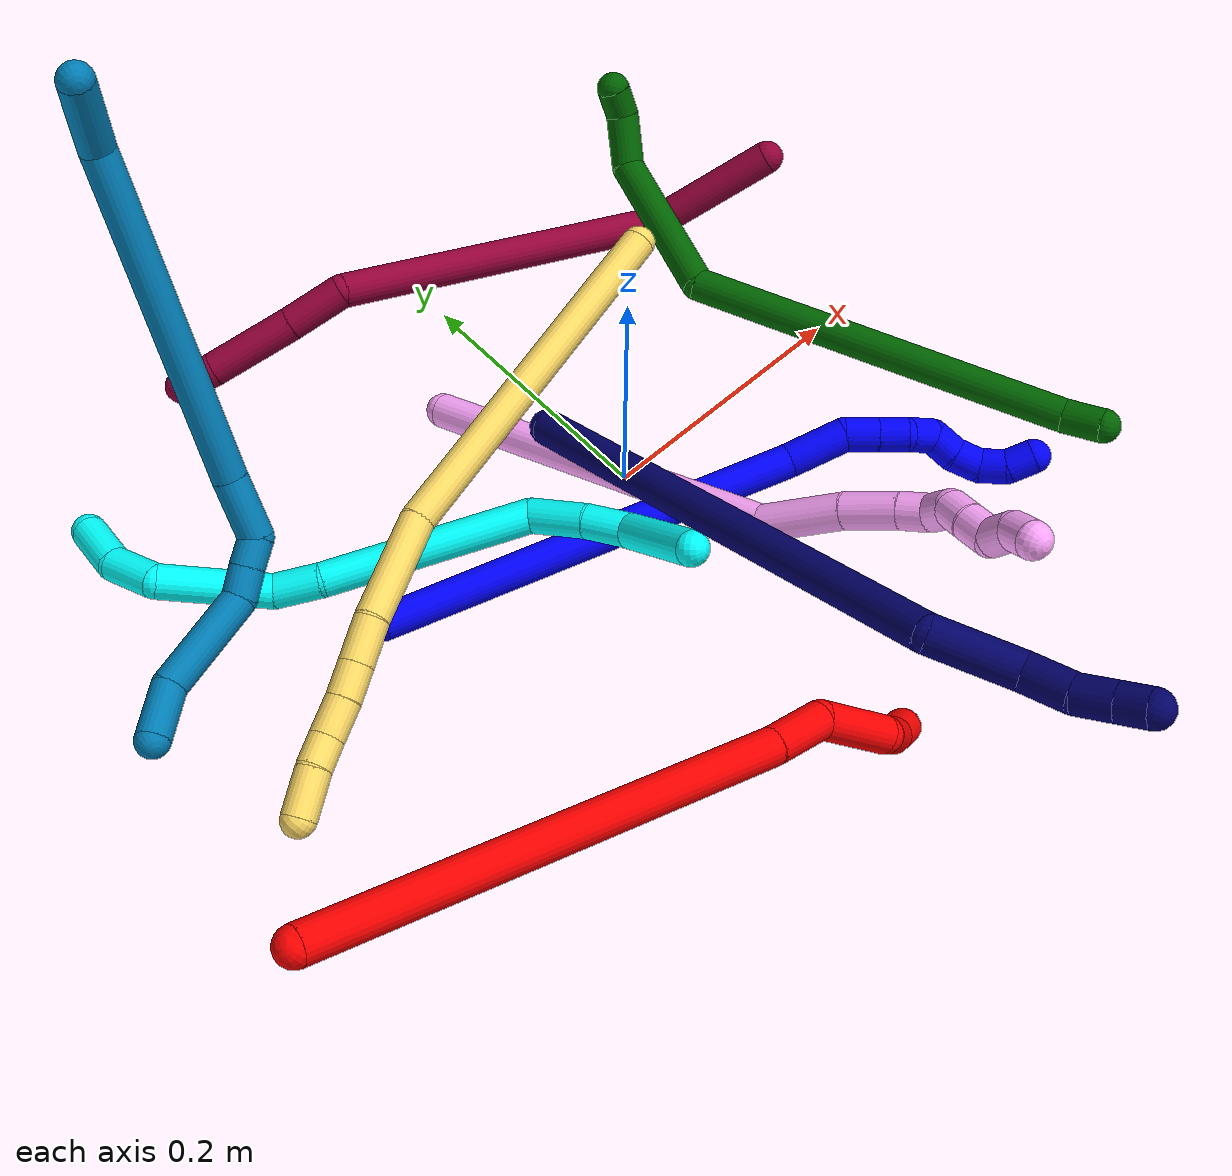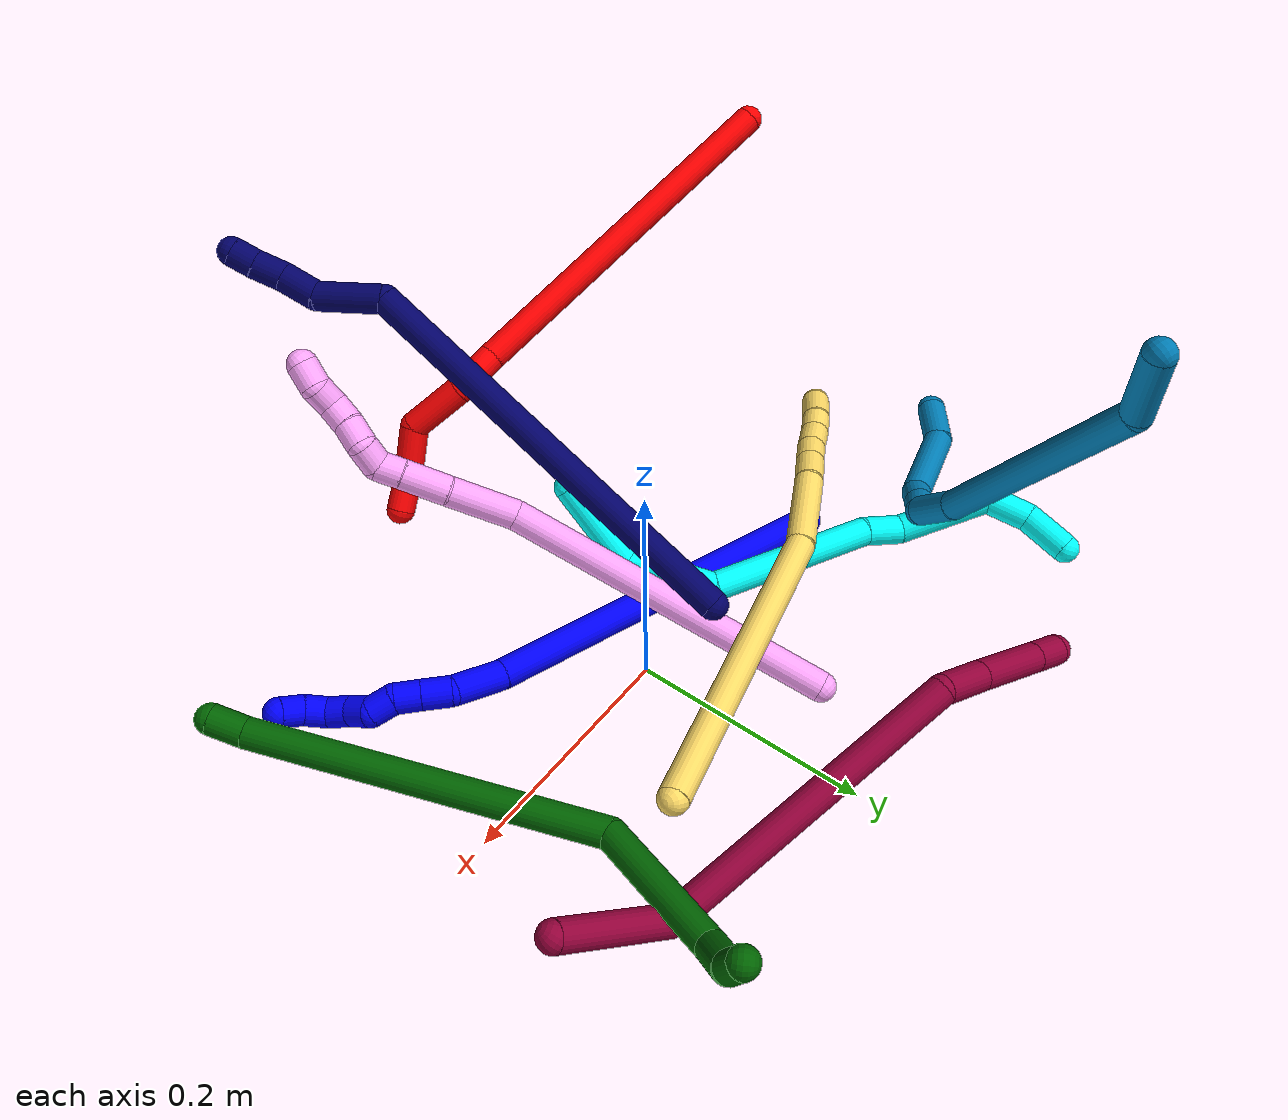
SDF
<sdf version="1.7">
 <world name="default">
  <plugin name="TubeGeneratorPlugin" filename="libtube_generator_plugin.so"/>
  <model name="photoneo_s_sensor">
   <static>1</static>
   <pose>0 0 2 1.57079 1.57079 3.14159</pose>
   <link name="link">
    <inertial><mass>0.1</mass></inertial>
    <sensor name="sensor" type="depth">
     <update_rate>30</update_rate>
     <camera>
      <horizontal_fov>1.22</horizontal_fov>
      <image><width>1920</width><height>1200</height><format>B8G8R8</format></image>
      <clip><near>0.1</near><far>4</far></clip>
      <depth_camera><output>points</output></depth_camera>
     </camera>
     <plugin name="camera_plugin" filename="libgazebo_ros_depth_camera.so">
      <baseline>0.2</baseline>
      <alwaysOn>1</alwaysOn>
      <updateRate>0.0</updateRate>
      <cameraName>camera_ir</cameraName>
      <imageTopicName>/camera/color/image_raw</imageTopicName>
      <cameraInfoTopicName>/camera/color/camera_info</cameraInfoTopicName>
      <depthImageTopicName>/camera/depth/image_raw</depthImageTopicName>
      <depthImageCameraInfoTopicName>/camera/depth/camera_info</depthImageCameraInfoTopicName>
      <pointCloudTopicName>/camera/depth/points</pointCloudTopicName>
      <frameName>fr_optical</frameName>
      <pointCloudCutoff>0.1</pointCloudCutoff>
      <pointCloudCutoffMax>2.0</pointCloudCutoffMax>
      <distortionK1>0</distortionK1>
      <distortionK2>0</distortionK2>
      <distortionK3>0</distortionK3>
      <distortionT1>0</distortionT1>
      <distortionT2>0</distortionT2>
      <CxPrime>0</CxPrime>
      <Cx>0</Cx>
      <Cy>0</Cy>
      <focalLength>0</focalLength>
      <hackBaseline>0</hackBaseline>
     </plugin>
    </sensor>
   </link>
  </model>
  <gravity>0 0 -9.8</gravity>
  <magnetic_field>6e-06 2.3e-05 -4.2e-05</magnetic_field>
  <atmosphere type="adiabatic"/>
  <physics name="default_physics" default="0" type="ode">
   <max_step_size>0.003</max_step_size>
   <real_time_factor>1</real_time_factor>
   <real_time_update_rate>1000</real_time_update_rate>
   <max_contacts>10000</max_contacts>
   <ode>
    <solver>
     <type>quick</type>
     <iters>100</iters>
     <sor>1.3</sor>
     <use_dynamic_moi_rescaling>0</use_dynamic_moi_rescaling>
    </solver>
    <constraints>
     <contact_max_correcting_vel>0</contact_max_correcting_vel>
     <contact_surface_layer>0.001</contact_surface_layer>
     <cfm>0</cfm>
     <erp>0.2</erp>
    </constraints>
   </ode>
  </physics>
  <scene><ambient>0.4 0.4 0.4 1</ambient><background>0.7 0.7 0.7 1</background><shadows>0</shadows></scene>
  <audio><device>default</device></audio>
  <spherical_coordinates>
   <surface_model>EARTH_WGS84</surface_model>
   <latitude_deg>0</latitude_deg>
   <longitude_deg>0</longitude_deg>
   <elevation>0</elevation>
   <heading_deg>0</heading_deg>
  </spherical_coordinates>
  <model name="bin">
   <static>1</static>
   <link name="bottom">
    <collision name="collision-bottom">
     <pose>0 0 -0.01 0 -0 0</pose>
     <geometry><box><size>0.8 0.6 0.02</size></box></geometry>
     <surface>
      <friction><ode><mu>100</mu><mu2>100</mu2></ode></friction>
      <contact><collide_bitmask>65535</collide_bitmask></contact>
     </surface>
    </collision>
   </link>
   <link name="west_wall">
    <collision name="collision-west_wall">
     <pose>-0.41 0 0.1 0 -0 0</pose>
     <geometry><box><size>0.02 0.6 0.2</size></box></geometry>
     <surface>
      <friction><ode><mu>100</mu><mu2>100</mu2></ode></friction>
      <contact><collide_bitmask>65535</collide_bitmask></contact>
     </surface>
    </collision>
   </link>
   <link name="east_wall">
    <collision name="collision-east_wall">
     <pose>0.41 0 0.1 0 -0 0</pose>
     <geometry><box><size>0.02 0.6 0.2</size></box></geometry>
     <surface>
      <friction><ode><mu>100</mu><mu2>100</mu2></ode></friction>
      <contact><collide_bitmask>65535</collide_bitmask></contact>
     </surface>
    </collision>
   </link>
   <link name="south_wall">
    <collision name="collision-south_wall">
     <pose>0 -0.31 0.1 0 -0 0</pose>
     <geometry><box><size>0.8 0.02 0.2</size></box></geometry>
     <surface>
      <friction><ode><mu>100</mu><mu2>100</mu2></ode></friction>
      <contact><collide_bitmask>65535</collide_bitmask></contact>
     </surface>
    </collision>
   </link>
   <link name="north_wall">
    <collision name="collision-north_wall">
     <pose>0 0.31 0.1 0 -0 0</pose>
     <geometry><box><size>0.8 0.02 0.2</size></box></geometry>
     <surface>
      <friction><ode><mu>100</mu><mu2>100</mu2></ode></friction>
      <contact><collide_bitmask>65535</collide_bitmask></contact>
     </surface>
    </collision>
   </link>
  </model>
  <model name="1">
   <static>0</static>
   <link name="1">
    <collision name="collision-cylinder-e_1_1_4">
     <pose>0.152518 -0.024412 0.013199 1.07513 1.39081 0.923204</pose>
     <geometry><cylinder><radius>0.0125</radius><length>0.310044</length></cylinder></geometry>
     <surface>
      <friction><ode><mu>1.16</mu><mu2>1.16</mu2><slip1>0</slip1><slip2>0</slip2></ode></friction>
      <contact><ode><kp>1e+06</kp><kd>1</kd><max_vel>0</max_vel><min_depth>0.001</min_depth></ode></contact>
     </surface>
    </collision>
    <visual name="visual-cylinder-e_1_1_4">
     <pose>0.152518 -0.024412 0.013199 1.07513 1.39081 0.923204</pose>
     <geometry><cylinder><radius>0.0125</radius><length>0.310044</length></cylinder></geometry>
     <material><ambient>0 0 1 1</ambient></material>
    </visual>
    <collision name="collision-cylinder-e_2_4_5">
     <pose>0.326845 -0.048258 0.029204 -0.19883 1.4403 -0.174573</pose>
     <geometry><cylinder><radius>0.0125</radius><length>0.043993</length></cylinder></geometry>
     <surface>
      <friction><ode><mu>1.16</mu><mu2>1.16</mu2><slip1>0</slip1><slip2>0</slip2></ode></friction>
      <contact><ode><kp>1e+06</kp><kd>1</kd><max_vel>0</max_vel><min_depth>0.001</min_depth></ode></contact>
     </surface>
    </collision>
    <visual name="visual-cylinder-e_2_4_5">
     <pose>0.326845 -0.048258 0.029204 -0.19883 1.4403 -0.174573</pose>
     <geometry><cylinder><radius>0.0125</radius><length>0.043993</length></cylinder></geometry>
     <material><ambient>0 0 1 1</ambient></material>
    </visual>
    <collision name="collision-cylinder-e_3_5_6">
     <pose>0.358941 -0.049687 0.03807 0.317903 1.01564 0.177947</pose>
     <geometry><cylinder><radius>0.0125</radius><length>0.024208</length></cylinder></geometry>
     <surface>
      <friction><ode><mu>1.16</mu><mu2>1.16</mu2><slip1>0</slip1><slip2>0</slip2></ode></friction>
      <contact><ode><kp>1e+06</kp><kd>1</kd><max_vel>0</max_vel><min_depth>0.001</min_depth></ode></contact>
     </surface>
    </collision>
    <visual name="visual-cylinder-e_3_5_6">
     <pose>0.358941 -0.049687 0.03807 0.317903 1.01564 0.177947</pose>
     <geometry><cylinder><radius>0.0125</radius><length>0.024208</length></cylinder></geometry>
     <material><ambient>0 0 1 1</ambient></material>
    </visual>
    <collision name="collision-cylinder-e_4_6_7">
     <pose>0.378259 -0.053431 0.049231 0.330544 1.03253 0.188786</pose>
     <geometry><cylinder><radius>0.0125</radius><length>0.021038</length></cylinder></geometry>
     <surface>
      <friction><ode><mu>1.16</mu><mu2>1.16</mu2><slip1>0</slip1><slip2>0</slip2></ode></friction>
      <contact><ode><kp>1e+06</kp><kd>1</kd><max_vel>0</max_vel><min_depth>0.001</min_depth></ode></contact>
     </surface>
    </collision>
    <visual name="visual-cylinder-e_4_6_7">
     <pose>0.378259 -0.053431 0.049231 0.330544 1.03253 0.188786</pose>
     <geometry><cylinder><radius>0.0125</radius><length>0.021038</length></cylinder></geometry>
     <material><ambient>0 0 1 1</ambient></material>
    </visual>
    <collision name="collision-cylinder-e_5_7_8">
     <pose>0.395497 -0.060514 0.057035 1.10159 0.941165 0.605662</pose>
     <geometry><cylinder><radius>0.0125</radius><length>0.020307</length></cylinder></geometry>
     <surface>
      <friction><ode><mu>1.16</mu><mu2>1.16</mu2><slip1>0</slip1><slip2>0</slip2></ode></friction>
      <contact><ode><kp>1e+06</kp><kd>1</kd><max_vel>0</max_vel><min_depth>0.001</min_depth></ode></contact>
     </surface>
    </collision>
    <visual name="visual-cylinder-e_5_7_8">
     <pose>0.395497 -0.060514 0.057035 1.10159 0.941165 0.605662</pose>
     <geometry><cylinder><radius>0.0125</radius><length>0.020307</length></cylinder></geometry>
     <material><ambient>0 0 1 1</ambient></material>
    </visual>
    <collision name="collision-cylinder-e_6_8_9">
     <pose>0.407021 -0.071061 0.067745 0.57723 0.334154 0.100062</pose>
     <geometry><cylinder><radius>0.0125</radius><length>0.020227</length></cylinder></geometry>
     <surface>
      <friction><ode><mu>1.16</mu><mu2>1.16</mu2><slip1>0</slip1><slip2>0</slip2></ode></friction>
      <contact><ode><kp>1e+06</kp><kd>1</kd><max_vel>0</max_vel><min_depth>0.001</min_depth></ode></contact>
     </surface>
    </collision>
    <visual name="visual-cylinder-e_6_8_9">
     <pose>0.407021 -0.071061 0.067745 0.57723 0.334154 0.100062</pose>
     <geometry><cylinder><radius>0.0125</radius><length>0.020227</length></cylinder></geometry>
     <material><ambient>0 0 1 1</ambient></material>
    </visual>
    <collision name="collision-cylinder-e_7_9_10">
     <pose>0.416218 -0.080391 0.082837 0.526229 0.622373 0.17284</pose>
     <geometry><cylinder><radius>0.0125</radius><length>0.020173</length></cylinder></geometry>
     <surface>
      <friction><ode><mu>1.16</mu><mu2>1.16</mu2><slip1>0</slip1><slip2>0</slip2></ode></friction>
      <contact><ode><kp>1e+06</kp><kd>1</kd><max_vel>0</max_vel><min_depth>0.001</min_depth></ode></contact>
     </surface>
    </collision>
    <visual name="visual-cylinder-e_7_9_10">
     <pose>0.416218 -0.080391 0.082837 0.526229 0.622373 0.17284</pose>
     <geometry><cylinder><radius>0.0125</radius><length>0.020173</length></cylinder></geometry>
     <material><ambient>0 0 1 1</ambient></material>
    </visual>
    <collision name="collision-cylinder-e_8_10_11">
     <pose>0.429927 -0.084499 0.09615 -0.001333 0.898996 -0.000643</pose>
     <geometry><cylinder><radius>0.0125</radius><length>0.020007</length></cylinder></geometry>
     <surface>
      <friction><ode><mu>1.16</mu><mu2>1.16</mu2><slip1>0</slip1><slip2>0</slip2></ode></friction>
      <contact><ode><kp>1e+06</kp><kd>1</kd><max_vel>0</max_vel><min_depth>0.001</min_depth></ode></contact>
     </surface>
    </collision>
    <visual name="visual-cylinder-e_8_10_11">
     <pose>0.429927 -0.084499 0.09615 -0.001333 0.898996 -0.000643</pose>
     <geometry><cylinder><radius>0.0125</radius><length>0.020007</length></cylinder></geometry>
     <material><ambient>0 0 1 1</ambient></material>
    </visual>
    <collision name="collision-cylinder-e_9_11_2">
     <pose>0.447282 -0.082867 0.10496 -0.560971 1.26072 -0.414371</pose>
     <geometry><cylinder><radius>0.0125</radius><length>0.020002</length></cylinder></geometry>
     <surface>
      <friction><ode><mu>1.16</mu><mu2>1.16</mu2><slip1>0</slip1><slip2>0</slip2></ode></friction>
      <contact><ode><kp>1e+06</kp><kd>1</kd><max_vel>0</max_vel><min_depth>0.001</min_depth></ode></contact>
     </surface>
    </collision>
    <visual name="visual-cylinder-e_9_11_2">
     <pose>0.447282 -0.082867 0.10496 -0.560971 1.26072 -0.414371</pose>
     <geometry><cylinder><radius>0.0125</radius><length>0.020002</length></cylinder></geometry>
     <material><ambient>0 0 1 1</ambient></material>
    </visual>
    <collision name="collision-sphere-2">
     <pose>0.456806 -0.081243 0.107544 0 -0 0</pose>
     <geometry><sphere><radius>0.0125</radius></sphere></geometry>
     <surface>
      <friction><ode><mu>1.16</mu><mu2>1.16</mu2><slip1>0</slip1><slip2>0</slip2></ode></friction>
      <contact><ode><kp>1e+06</kp><kd>1</kd><max_vel>0</max_vel><min_depth>0.001</min_depth></ode></contact>
     </surface>
    </collision>
    <visual name="visual-sphere-2">
     <pose>0.456806 -0.081243 0.107544 0 -0 0</pose>
     <geometry><sphere><radius>0.0125</radius></sphere></geometry>
     <material><ambient>0 0 1 1</ambient></material>
    </visual>
    <collision name="collision-sphere-11">
     <pose>0.437757 -0.08449 0.102376 0 -0 0</pose>
     <geometry><sphere><radius>0.0125</radius></sphere></geometry>
     <surface>
      <friction><ode><mu>1.16</mu><mu2>1.16</mu2><slip1>0</slip1><slip2>0</slip2></ode></friction>
      <contact><ode><kp>1e+06</kp><kd>1</kd><max_vel>0</max_vel><min_depth>0.001</min_depth></ode></contact>
     </surface>
    </collision>
    <visual name="visual-sphere-11">
     <pose>0.437757 -0.08449 0.102376 0 -0 0</pose>
     <geometry><sphere><radius>0.0125</radius></sphere></geometry>
     <material><ambient>0 0 1 1</ambient></material>
    </visual>
    <collision name="collision-sphere-10">
     <pose>0.422098 -0.084507 0.089924 0 -0 0</pose>
     <geometry><sphere><radius>0.0125</radius></sphere></geometry>
     <surface>
      <friction><ode><mu>1.16</mu><mu2>1.16</mu2><slip1>0</slip1><slip2>0</slip2></ode></friction>
      <contact><ode><kp>1e+06</kp><kd>1</kd><max_vel>0</max_vel><min_depth>0.001</min_depth></ode></contact>
     </surface>
    </collision>
    <visual name="visual-sphere-10">
     <pose>0.422098 -0.084507 0.089924 0 -0 0</pose>
     <geometry><sphere><radius>0.0125</radius></sphere></geometry>
     <material><ambient>0 0 1 1</ambient></material>
    </visual>
    <collision name="collision-sphere-9">
     <pose>0.410338 -0.076275 0.075751 0 -0 0</pose>
     <geometry><sphere><radius>0.0125</radius></sphere></geometry>
     <surface>
      <friction><ode><mu>1.16</mu><mu2>1.16</mu2><slip1>0</slip1><slip2>0</slip2></ode></friction>
      <contact><ode><kp>1e+06</kp><kd>1</kd><max_vel>0</max_vel><min_depth>0.001</min_depth></ode></contact>
     </surface>
    </collision>
    <visual name="visual-sphere-9">
     <pose>0.410338 -0.076275 0.075751 0 -0 0</pose>
     <geometry><sphere><radius>0.0125</radius></sphere></geometry>
     <material><ambient>0 0 1 1</ambient></material>
    </visual>
    <collision name="collision-sphere-4">
     <pose>0.305036 -0.048824 0.026398 0 -0 0</pose>
     <geometry><sphere><radius>0.0125</radius></sphere></geometry>
     <surface>
      <friction><ode><mu>1.16</mu><mu2>1.16</mu2><slip1>0</slip1><slip2>0</slip2></ode></friction>
      <contact><ode><kp>1e+06</kp><kd>1</kd><max_vel>0</max_vel><min_depth>0.001</min_depth></ode></contact>
     </surface>
    </collision>
    <visual name="visual-sphere-4">
     <pose>0.305036 -0.048824 0.026398 0 -0 0</pose>
     <geometry><sphere><radius>0.0125</radius></sphere></geometry>
     <material><ambient>0 0 1 1</ambient></material>
    </visual>
    <collision name="collision-sphere-1">
     <geometry><sphere><radius>0.0125</radius></sphere></geometry>
     <surface>
      <friction><ode><mu>1.16</mu><mu2>1.16</mu2><slip1>0</slip1><slip2>0</slip2></ode></friction>
      <contact><ode><kp>1e+06</kp><kd>1</kd><max_vel>0</max_vel><min_depth>0.001</min_depth></ode></contact>
     </surface>
    </collision>
    <visual name="visual-sphere-1">
     <geometry><sphere><radius>0.0125</radius></sphere></geometry>
     <material><ambient>0 0 1 1</ambient></material>
    </visual>
    <collision name="collision-sphere-8">
     <pose>0.403704 -0.065847 0.059739 0 -0 0</pose>
     <geometry><sphere><radius>0.0125</radius></sphere></geometry>
     <surface>
      <friction><ode><mu>1.16</mu><mu2>1.16</mu2><slip1>0</slip1><slip2>0</slip2></ode></friction>
      <contact><ode><kp>1e+06</kp><kd>1</kd><max_vel>0</max_vel><min_depth>0.001</min_depth></ode></contact>
     </surface>
    </collision>
    <visual name="visual-sphere-8">
     <pose>0.403704 -0.065847 0.059739 0 -0 0</pose>
     <geometry><sphere><radius>0.0125</radius></sphere></geometry>
     <material><ambient>0 0 1 1</ambient></material>
    </visual>
    <collision name="collision-sphere-5">
     <pose>0.348654 -0.047693 0.03201 0 -0 0</pose>
     <geometry><sphere><radius>0.0125</radius></sphere></geometry>
     <surface>
      <friction><ode><mu>1.16</mu><mu2>1.16</mu2><slip1>0</slip1><slip2>0</slip2></ode></friction>
      <contact><ode><kp>1e+06</kp><kd>1</kd><max_vel>0</max_vel><min_depth>0.001</min_depth></ode></contact>
     </surface>
    </collision>
    <visual name="visual-sphere-5">
     <pose>0.348654 -0.047693 0.03201 0 -0 0</pose>
     <geometry><sphere><radius>0.0125</radius></sphere></geometry>
     <material><ambient>0 0 1 1</ambient></material>
    </visual>
    <collision name="collision-sphere-6">
     <pose>0.369227 -0.051681 0.04413 0 -0 0</pose>
     <geometry><sphere><radius>0.0125</radius></sphere></geometry>
     <surface>
      <friction><ode><mu>1.16</mu><mu2>1.16</mu2><slip1>0</slip1><slip2>0</slip2></ode></friction>
      <contact><ode><kp>1e+06</kp><kd>1</kd><max_vel>0</max_vel><min_depth>0.001</min_depth></ode></contact>
     </surface>
    </collision>
    <visual name="visual-sphere-6">
     <pose>0.369227 -0.051681 0.04413 0 -0 0</pose>
     <geometry><sphere><radius>0.0125</radius></sphere></geometry>
     <material><ambient>0 0 1 1</ambient></material>
    </visual>
    <collision name="collision-sphere-7">
     <pose>0.387291 -0.055182 0.054332 0 -0 0</pose>
     <geometry><sphere><radius>0.0125</radius></sphere></geometry>
     <surface>
      <friction><ode><mu>1.16</mu><mu2>1.16</mu2><slip1>0</slip1><slip2>0</slip2></ode></friction>
      <contact><ode><kp>1e+06</kp><kd>1</kd><max_vel>0</max_vel><min_depth>0.001</min_depth></ode></contact>
     </surface>
    </collision>
    <visual name="visual-sphere-7">
     <pose>0.387291 -0.055182 0.054332 0 -0 0</pose>
     <geometry><sphere><radius>0.0125</radius></sphere></geometry>
     <material><ambient>0 0 1 1</ambient></material>
    </visual>
    <inertial>
     <pose>0.241044 -0.039309 0.031114 0 -0 0</pose>
     <mass>0.5</mass>
     <inertia>
      <ixx>0.00067</ixx>
      <ixy>0</ixy>
      <ixz>0</ixz>
      <iyy>0.002809</iyy>
      <iyz>0</iyz>
      <izz>-0.002069</izz>
     </inertia>
    </inertial>
   </link>
   <pose>-0.208086 0.019272 0.011496 1.53841 -0.190853 -0.232831</pose>
  </model>
  <model name="2">
   <static>0</static>
   <link name="2">
    <collision name="collision-cylinder-e_1_1_4">
     <pose>0.107705 -0.02603 -0.121108 2.92988 0.715691 2.5879</pose>
     <geometry><cylinder><radius>0.0125</radius><length>0.328298</length></cylinder></geometry>
     <surface>
      <friction><ode><mu>1.16</mu><mu2>1.16</mu2><slip1>0</slip1><slip2>0</slip2></ode></friction>
      <contact><ode><kp>1e+06</kp><kd>1</kd><max_vel>0</max_vel><min_depth>0.001</min_depth></ode></contact>
     </surface>
    </collision>
    <visual name="visual-cylinder-e_1_1_4">
     <pose>0.107705 -0.02603 -0.121108 2.92988 0.715691 2.5879</pose>
     <geometry><cylinder><radius>0.0125</radius><length>0.328298</length></cylinder></geometry>
     <material><ambient>1 0 0 1</ambient></material>
    </visual>
    <collision name="collision-cylinder-e_2_4_5">
     <pose>0.229819 -0.053745 -0.256593 3.02493 0.783083 2.86057</pose>
     <geometry><cylinder><radius>0.0125</radius><length>0.040851</length></cylinder></geometry>
     <surface>
      <friction><ode><mu>1.16</mu><mu2>1.16</mu2><slip1>0</slip1><slip2>0</slip2></ode></friction>
      <contact><ode><kp>1e+06</kp><kd>1</kd><max_vel>0</max_vel><min_depth>0.001</min_depth></ode></contact>
     </surface>
    </collision>
    <visual name="visual-cylinder-e_2_4_5">
     <pose>0.229819 -0.053745 -0.256593 3.02493 0.783083 2.86057</pose>
     <geometry><cylinder><radius>0.0125</radius><length>0.040851</length></cylinder></geometry>
     <material><ambient>1 0 0 1</ambient></material>
    </visual>
    <collision name="collision-cylinder-e_3_5_6">
     <pose>0.250804 -0.065386 -0.294907 2.74741 0.248418 1.11755</pose>
     <geometry><cylinder><radius>0.0125</radius><length>0.053489</length></cylinder></geometry>
     <surface>
      <friction><ode><mu>1.16</mu><mu2>1.16</mu2><slip1>0</slip1><slip2>0</slip2></ode></friction>
      <contact><ode><kp>1e+06</kp><kd>1</kd><max_vel>0</max_vel><min_depth>0.001</min_depth></ode></contact>
     </surface>
    </collision>
    <visual name="visual-cylinder-e_3_5_6">
     <pose>0.250804 -0.065386 -0.294907 2.74741 0.248418 1.11755</pose>
     <geometry><cylinder><radius>0.0125</radius><length>0.053489</length></cylinder></geometry>
     <material><ambient>1 0 0 1</ambient></material>
    </visual>
    <collision name="collision-cylinder-e_4_6_7">
     <pose>0.258706 -0.067836 -0.341852 -2.82624 0.054732 -0.340984</pose>
     <geometry><cylinder><radius>0.0125</radius><length>0.048479</length></cylinder></geometry>
     <surface>
      <friction><ode><mu>1.16</mu><mu2>1.16</mu2><slip1>0</slip1><slip2>0</slip2></ode></friction>
      <contact><ode><kp>1e+06</kp><kd>1</kd><max_vel>0</max_vel><min_depth>0.001</min_depth></ode></contact>
     </surface>
    </collision>
    <visual name="visual-cylinder-e_4_6_7">
     <pose>0.258706 -0.067836 -0.341852 -2.82624 0.054732 -0.340984</pose>
     <geometry><cylinder><radius>0.0125</radius><length>0.048479</length></cylinder></geometry>
     <material><ambient>1 0 0 1</ambient></material>
    </visual>
    <collision name="collision-cylinder-e_5_7_2">
     <pose>0.264198 -0.055876 -0.377953 -2.81371 0.292644 -1.4555</pose>
     <geometry><cylinder><radius>0.0125</radius><length>0.028883</length></cylinder></geometry>
     <surface>
      <friction><ode><mu>1.16</mu><mu2>1.16</mu2><slip1>0</slip1><slip2>0</slip2></ode></friction>
      <contact><ode><kp>1e+06</kp><kd>1</kd><max_vel>0</max_vel><min_depth>0.001</min_depth></ode></contact>
     </surface>
    </collision>
    <visual name="visual-cylinder-e_5_7_2">
     <pose>0.264198 -0.055876 -0.377953 -2.81371 0.292644 -1.4555</pose>
     <geometry><cylinder><radius>0.0125</radius><length>0.028883</length></cylinder></geometry>
     <material><ambient>1 0 0 1</ambient></material>
    </visual>
    <collision name="collision-sphere-2">
     <pose>0.268364 -0.051423 -0.391043 0 -0 0</pose>
     <geometry><sphere><radius>0.0125</radius></sphere></geometry>
     <surface>
      <friction><ode><mu>1.16</mu><mu2>1.16</mu2><slip1>0</slip1><slip2>0</slip2></ode></friction>
      <contact><ode><kp>1e+06</kp><kd>1</kd><max_vel>0</max_vel><min_depth>0.001</min_depth></ode></contact>
     </surface>
    </collision>
    <visual name="visual-sphere-2">
     <pose>0.268364 -0.051423 -0.391043 0 -0 0</pose>
     <geometry><sphere><radius>0.0125</radius></sphere></geometry>
     <material><ambient>1 0 0 1</ambient></material>
    </visual>
    <collision name="collision-sphere-7">
     <pose>0.260032 -0.060329 -0.364862 0 -0 0</pose>
     <geometry><sphere><radius>0.0125</radius></sphere></geometry>
     <surface>
      <friction><ode><mu>1.16</mu><mu2>1.16</mu2><slip1>0</slip1><slip2>0</slip2></ode></friction>
      <contact><ode><kp>1e+06</kp><kd>1</kd><max_vel>0</max_vel><min_depth>0.001</min_depth></ode></contact>
     </surface>
    </collision>
    <visual name="visual-sphere-7">
     <pose>0.260032 -0.060329 -0.364862 0 -0 0</pose>
     <geometry><sphere><radius>0.0125</radius></sphere></geometry>
     <material><ambient>1 0 0 1</ambient></material>
    </visual>
    <collision name="collision-sphere-6">
     <pose>0.25738 -0.075342 -0.318842 0 -0 0</pose>
     <geometry><sphere><radius>0.0125</radius></sphere></geometry>
     <surface>
      <friction><ode><mu>1.16</mu><mu2>1.16</mu2><slip1>0</slip1><slip2>0</slip2></ode></friction>
      <contact><ode><kp>1e+06</kp><kd>1</kd><max_vel>0</max_vel><min_depth>0.001</min_depth></ode></contact>
     </surface>
    </collision>
    <visual name="visual-sphere-6">
     <pose>0.25738 -0.075342 -0.318842 0 -0 0</pose>
     <geometry><sphere><radius>0.0125</radius></sphere></geometry>
     <material><ambient>1 0 0 1</ambient></material>
    </visual>
    <collision name="collision-sphere-5">
     <pose>0.244228 -0.05543 -0.270971 0 -0 0</pose>
     <geometry><sphere><radius>0.0125</radius></sphere></geometry>
     <surface>
      <friction><ode><mu>1.16</mu><mu2>1.16</mu2><slip1>0</slip1><slip2>0</slip2></ode></friction>
      <contact><ode><kp>1e+06</kp><kd>1</kd><max_vel>0</max_vel><min_depth>0.001</min_depth></ode></contact>
     </surface>
    </collision>
    <visual name="visual-sphere-5">
     <pose>0.244228 -0.05543 -0.270971 0 -0 0</pose>
     <geometry><sphere><radius>0.0125</radius></sphere></geometry>
     <material><ambient>1 0 0 1</ambient></material>
    </visual>
    <collision name="collision-sphere-1">
     <geometry><sphere><radius>0.0125</radius></sphere></geometry>
     <surface>
      <friction><ode><mu>1.16</mu><mu2>1.16</mu2><slip1>0</slip1><slip2>0</slip2></ode></friction>
      <contact><ode><kp>1e+06</kp><kd>1</kd><max_vel>0</max_vel><min_depth>0.001</min_depth></ode></contact>
     </surface>
    </collision>
    <visual name="visual-sphere-1">
     <geometry><sphere><radius>0.0125</radius></sphere></geometry>
     <material><ambient>1 0 0 1</ambient></material>
    </visual>
    <collision name="collision-sphere-4">
     <pose>0.215409 -0.05206 -0.242215 0 -0 0</pose>
     <geometry><sphere><radius>0.0125</radius></sphere></geometry>
     <surface>
      <friction><ode><mu>1.16</mu><mu2>1.16</mu2><slip1>0</slip1><slip2>0</slip2></ode></friction>
      <contact><ode><kp>1e+06</kp><kd>1</kd><max_vel>0</max_vel><min_depth>0.001</min_depth></ode></contact>
     </surface>
    </collision>
    <visual name="visual-sphere-4">
     <pose>0.215409 -0.05206 -0.242215 0 -0 0</pose>
     <geometry><sphere><radius>0.0125</radius></sphere></geometry>
     <material><ambient>1 0 0 1</ambient></material>
    </visual>
    <inertial>
     <pose>0.156671 -0.038282 -0.18701 0 -0 0</pose>
     <mass>0.5</mass>
     <inertia>
      <ixx>-0.000685</ixx>
      <ixy>0</ixy>
      <ixz>0</ixz>
      <iyy>0.003848</iyy>
      <iyz>0</iyz>
      <izz>-0.001513</izz>
     </inertia>
    </inertial>
   </link>
   <pose>-0.427054 -0.202244 0.222027 -0.260514 -0.454034 0.187476</pose>
  </model>
  <model name="3">
   <static>0</static>
   <link name="3">
    <collision name="collision-cylinder-e_1_1_4">
     <pose>0.022582 -0.002578 0.031527 0.081576 0.619987 0.026143</pose>
     <geometry><cylinder><radius>0.0125</radius><length>0.077731</length></cylinder></geometry>
     <surface>
      <friction><ode><mu>1.16</mu><mu2>1.16</mu2><slip1>0</slip1><slip2>0</slip2></ode></friction>
      <contact><ode><kp>1e+06</kp><kd>1</kd><max_vel>0</max_vel><min_depth>0.001</min_depth></ode></contact>
     </surface>
    </collision>
    <visual name="visual-cylinder-e_1_1_4">
     <pose>0.022582 -0.002578 0.031527 0.081576 0.619987 0.026143</pose>
     <geometry><cylinder><radius>0.0125</radius><length>0.077731</length></cylinder></geometry>
     <material><ambient>0.003922 1 0.996078 1</ambient></material>
    </visual>
    <collision name="collision-cylinder-e_2_4_5">
     <pose>0.044304 -0.007715 0.078894 0.160226 -0.053531 -0.004299</pose>
     <geometry><cylinder><radius>0.0125</radius><length>0.032137</length></cylinder></geometry>
     <surface>
      <friction><ode><mu>1.16</mu><mu2>1.16</mu2><slip1>0</slip1><slip2>0</slip2></ode></friction>
      <contact><ode><kp>1e+06</kp><kd>1</kd><max_vel>0</max_vel><min_depth>0.001</min_depth></ode></contact>
     </surface>
    </collision>
    <visual name="visual-cylinder-e_2_4_5">
     <pose>0.044304 -0.007715 0.078894 0.160226 -0.053531 -0.004299</pose>
     <geometry><cylinder><radius>0.0125</radius><length>0.032137</length></cylinder></geometry>
     <material><ambient>0.003922 1 0.996078 1</ambient></material>
    </visual>
    <collision name="collision-cylinder-e_3_5_6">
     <pose>0.043959 -0.011299 0.116284 0.047477 0.023874 0.000567</pose>
     <geometry><cylinder><radius>0.0125</radius><length>0.043162</length></cylinder></geometry>
     <surface>
      <friction><ode><mu>1.16</mu><mu2>1.16</mu2><slip1>0</slip1><slip2>0</slip2></ode></friction>
      <contact><ode><kp>1e+06</kp><kd>1</kd><max_vel>0</max_vel><min_depth>0.001</min_depth></ode></contact>
     </surface>
    </collision>
    <visual name="visual-cylinder-e_3_5_6">
     <pose>0.043959 -0.011299 0.116284 0.047477 0.023874 0.000567</pose>
     <geometry><cylinder><radius>0.0125</radius><length>0.043162</length></cylinder></geometry>
     <material><ambient>0.003922 1 0.996078 1</ambient></material>
    </visual>
    <collision name="collision-cylinder-e_4_6_7">
     <pose>0.006353 0.010183 0.198918 -0.353014 -0.529759 0.096688</pose>
     <geometry><cylinder><radius>0.0125</radius><length>0.150877</length></cylinder></geometry>
     <surface>
      <friction><ode><mu>1.16</mu><mu2>1.16</mu2><slip1>0</slip1><slip2>0</slip2></ode></friction>
      <contact><ode><kp>1e+06</kp><kd>1</kd><max_vel>0</max_vel><min_depth>0.001</min_depth></ode></contact>
     </surface>
    </collision>
    <visual name="visual-cylinder-e_4_6_7">
     <pose>0.006353 0.010183 0.198918 -0.353014 -0.529759 0.096688</pose>
     <geometry><cylinder><radius>0.0125</radius><length>0.150877</length></cylinder></geometry>
     <material><ambient>0.003922 1 0.996078 1</ambient></material>
    </visual>
    <collision name="collision-cylinder-e_5_7_8">
     <pose>-0.036681 0.037104 0.276254 -0.26521 -0.28389 0.038119</pose>
     <geometry><cylinder><radius>0.0125</radius><length>0.035084</length></cylinder></geometry>
     <surface>
      <friction><ode><mu>1.16</mu><mu2>1.16</mu2><slip1>0</slip1><slip2>0</slip2></ode></friction>
      <contact><ode><kp>1e+06</kp><kd>1</kd><max_vel>0</max_vel><min_depth>0.001</min_depth></ode></contact>
     </surface>
    </collision>
    <visual name="visual-cylinder-e_5_7_8">
     <pose>-0.036681 0.037104 0.276254 -0.26521 -0.28389 0.038119</pose>
     <geometry><cylinder><radius>0.0125</radius><length>0.035084</length></cylinder></geometry>
     <material><ambient>0.003922 1 0.996078 1</ambient></material>
    </visual>
    <collision name="collision-cylinder-e_6_8_9">
     <pose>-0.065926 0.037622 0.324621 0.120714 -0.644837 -0.040371</pose>
     <geometry><cylinder><radius>0.0125</radius><length>0.08096</length></cylinder></geometry>
     <surface>
      <friction><ode><mu>1.16</mu><mu2>1.16</mu2><slip1>0</slip1><slip2>0</slip2></ode></friction>
      <contact><ode><kp>1e+06</kp><kd>1</kd><max_vel>0</max_vel><min_depth>0.001</min_depth></ode></contact>
     </surface>
    </collision>
    <visual name="visual-cylinder-e_6_8_9">
     <pose>-0.065926 0.037622 0.324621 0.120714 -0.644837 -0.040371</pose>
     <geometry><cylinder><radius>0.0125</radius><length>0.08096</length></cylinder></geometry>
     <material><ambient>0.003922 1 0.996078 1</ambient></material>
    </visual>
    <collision name="collision-cylinder-e_7_9_10">
     <pose>-0.08801 0.028973 0.375377 0.249661 0.116291 0.014609</pose>
     <geometry><cylinder><radius>0.0125</radius><length>0.038735</length></cylinder></geometry>
     <surface>
      <friction><ode><mu>1.16</mu><mu2>1.16</mu2><slip1>0</slip1><slip2>0</slip2></ode></friction>
      <contact><ode><kp>1e+06</kp><kd>1</kd><max_vel>0</max_vel><min_depth>0.001</min_depth></ode></contact>
     </surface>
    </collision>
    <visual name="visual-cylinder-e_7_9_10">
     <pose>-0.08801 0.028973 0.375377 0.249661 0.116291 0.014609</pose>
     <geometry><cylinder><radius>0.0125</radius><length>0.038735</length></cylinder></geometry>
     <material><ambient>0.003922 1 0.996078 1</ambient></material>
    </visual>
    <collision name="collision-cylinder-e_8_10_2">
     <pose>-0.078199 0.014383 0.410532 0.537257 0.374879 0.104329</pose>
     <geometry><cylinder><radius>0.0125</radius><length>0.041314</length></cylinder></geometry>
     <surface>
      <friction><ode><mu>1.16</mu><mu2>1.16</mu2><slip1>0</slip1><slip2>0</slip2></ode></friction>
      <contact><ode><kp>1e+06</kp><kd>1</kd><max_vel>0</max_vel><min_depth>0.001</min_depth></ode></contact>
     </surface>
    </collision>
    <visual name="visual-cylinder-e_8_10_2">
     <pose>-0.078199 0.014383 0.410532 0.537257 0.374879 0.104329</pose>
     <geometry><cylinder><radius>0.0125</radius><length>0.041314</length></cylinder></geometry>
     <material><ambient>0.003922 1 0.996078 1</ambient></material>
    </visual>
    <collision name="collision-sphere-2">
     <pose>-0.070635 0.004545 0.427046 0 -0 0</pose>
     <geometry><sphere><radius>0.0125</radius></sphere></geometry>
     <surface>
      <friction><ode><mu>1.16</mu><mu2>1.16</mu2><slip1>0</slip1><slip2>0</slip2></ode></friction>
      <contact><ode><kp>1e+06</kp><kd>1</kd><max_vel>0</max_vel><min_depth>0.001</min_depth></ode></contact>
     </surface>
    </collision>
    <visual name="visual-sphere-2">
     <pose>-0.070635 0.004545 0.427046 0 -0 0</pose>
     <geometry><sphere><radius>0.0125</radius></sphere></geometry>
     <material><ambient>0.003922 1 0.996078 1</ambient></material>
    </visual>
    <collision name="collision-sphere-10">
     <pose>-0.085762 0.02422 0.394018 0 -0 0</pose>
     <geometry><sphere><radius>0.0125</radius></sphere></geometry>
     <surface>
      <friction><ode><mu>1.16</mu><mu2>1.16</mu2><slip1>0</slip1><slip2>0</slip2></ode></friction>
      <contact><ode><kp>1e+06</kp><kd>1</kd><max_vel>0</max_vel><min_depth>0.001</min_depth></ode></contact>
     </surface>
    </collision>
    <visual name="visual-sphere-10">
     <pose>-0.085762 0.02422 0.394018 0 -0 0</pose>
     <geometry><sphere><radius>0.0125</radius></sphere></geometry>
     <material><ambient>0.003922 1 0.996078 1</ambient></material>
    </visual>
    <collision name="collision-sphere-9">
     <pose>-0.090257 0.033726 0.356737 0 -0 0</pose>
     <geometry><sphere><radius>0.0125</radius></sphere></geometry>
     <surface>
      <friction><ode><mu>1.16</mu><mu2>1.16</mu2><slip1>0</slip1><slip2>0</slip2></ode></friction>
      <contact><ode><kp>1e+06</kp><kd>1</kd><max_vel>0</max_vel><min_depth>0.001</min_depth></ode></contact>
     </surface>
    </collision>
    <visual name="visual-sphere-9">
     <pose>-0.090257 0.033726 0.356737 0 -0 0</pose>
     <geometry><sphere><radius>0.0125</radius></sphere></geometry>
     <material><ambient>0.003922 1 0.996078 1</ambient></material>
    </visual>
    <collision name="collision-sphere-4">
     <pose>0.045164 -0.005155 0.063054 0 -0 0</pose>
     <geometry><sphere><radius>0.0125</radius></sphere></geometry>
     <surface>
      <friction><ode><mu>1.16</mu><mu2>1.16</mu2><slip1>0</slip1><slip2>0</slip2></ode></friction>
      <contact><ode><kp>1e+06</kp><kd>1</kd><max_vel>0</max_vel><min_depth>0.001</min_depth></ode></contact>
     </surface>
    </collision>
    <visual name="visual-sphere-4">
     <pose>0.045164 -0.005155 0.063054 0 -0 0</pose>
     <geometry><sphere><radius>0.0125</radius></sphere></geometry>
     <material><ambient>0.003922 1 0.996078 1</ambient></material>
    </visual>
    <collision name="collision-sphere-1">
     <geometry><sphere><radius>0.0125</radius></sphere></geometry>
     <surface>
      <friction><ode><mu>1.16</mu><mu2>1.16</mu2><slip1>0</slip1><slip2>0</slip2></ode></friction>
      <contact><ode><kp>1e+06</kp><kd>1</kd><max_vel>0</max_vel><min_depth>0.001</min_depth></ode></contact>
     </surface>
    </collision>
    <visual name="visual-sphere-1">
     <geometry><sphere><radius>0.0125</radius></sphere></geometry>
     <material><ambient>0.003922 1 0.996078 1</ambient></material>
    </visual>
    <collision name="collision-sphere-8">
     <pose>-0.041594 0.041518 0.292505 0 -0 0</pose>
     <geometry><sphere><radius>0.0125</radius></sphere></geometry>
     <surface>
      <friction><ode><mu>1.16</mu><mu2>1.16</mu2><slip1>0</slip1><slip2>0</slip2></ode></friction>
      <contact><ode><kp>1e+06</kp><kd>1</kd><max_vel>0</max_vel><min_depth>0.001</min_depth></ode></contact>
     </surface>
    </collision>
    <visual name="visual-sphere-8">
     <pose>-0.041594 0.041518 0.292505 0 -0 0</pose>
     <geometry><sphere><radius>0.0125</radius></sphere></geometry>
     <material><ambient>0.003922 1 0.996078 1</ambient></material>
    </visual>
    <collision name="collision-sphere-5">
     <pose>0.043444 -0.010275 0.094734 0 -0 0</pose>
     <geometry><sphere><radius>0.0125</radius></sphere></geometry>
     <surface>
      <friction><ode><mu>1.16</mu><mu2>1.16</mu2><slip1>0</slip1><slip2>0</slip2></ode></friction>
      <contact><ode><kp>1e+06</kp><kd>1</kd><max_vel>0</max_vel><min_depth>0.001</min_depth></ode></contact>
     </surface>
    </collision>
    <visual name="visual-sphere-5">
     <pose>0.043444 -0.010275 0.094734 0 -0 0</pose>
     <geometry><sphere><radius>0.0125</radius></sphere></geometry>
     <material><ambient>0.003922 1 0.996078 1</ambient></material>
    </visual>
    <collision name="collision-sphere-6">
     <pose>0.044475 -0.012323 0.137834 0 -0 0</pose>
     <geometry><sphere><radius>0.0125</radius></sphere></geometry>
     <surface>
      <friction><ode><mu>1.16</mu><mu2>1.16</mu2><slip1>0</slip1><slip2>0</slip2></ode></friction>
      <contact><ode><kp>1e+06</kp><kd>1</kd><max_vel>0</max_vel><min_depth>0.001</min_depth></ode></contact>
     </surface>
    </collision>
    <visual name="visual-sphere-6">
     <pose>0.044475 -0.012323 0.137834 0 -0 0</pose>
     <geometry><sphere><radius>0.0125</radius></sphere></geometry>
     <material><ambient>0.003922 1 0.996078 1</ambient></material>
    </visual>
    <collision name="collision-sphere-7">
     <pose>-0.031768 0.03269 0.260002 0 -0 0</pose>
     <geometry><sphere><radius>0.0125</radius></sphere></geometry>
     <surface>
      <friction><ode><mu>1.16</mu><mu2>1.16</mu2><slip1>0</slip1><slip2>0</slip2></ode></friction>
      <contact><ode><kp>1e+06</kp><kd>1</kd><max_vel>0</max_vel><min_depth>0.001</min_depth></ode></contact>
     </surface>
    </collision>
    <visual name="visual-sphere-7">
     <pose>-0.031768 0.03269 0.260002 0 -0 0</pose>
     <geometry><sphere><radius>0.0125</radius></sphere></geometry>
     <material><ambient>0.003922 1 0.996078 1</ambient></material>
    </visual>
    <inertial>
     <pose>-0.014458 0.013329 0.214983 0 -0 0</pose>
     <mass>0.5</mass>
     <inertia>
      <ixx>0.000373</ixx>
      <ixy>0</ixy>
      <ixz>0</ixz>
      <iyy>0.000422</iyy>
      <iyz>0</iyz>
      <izz>0.000108</izz>
     </inertia>
    </inertial>
   </link>
   <pose>-0.051079 -0.116817 0.099664 -2.0619 0.823235 0.178486</pose>
  </model>
  <model name="4">
   <static>0</static>
   <link name="4">
    <collision name="collision-cylinder-e_1_1_4">
     <pose>0.005321 -0.041121 0.133983 0.297786 0.037946 0.005693</pose>
     <geometry><cylinder><radius>0.0125</radius><length>0.280504</length></cylinder></geometry>
     <surface>
      <friction><ode><mu>1.16</mu><mu2>1.16</mu2><slip1>0</slip1><slip2>0</slip2></ode></friction>
      <contact><ode><kp>1e+06</kp><kd>1</kd><max_vel>0</max_vel><min_depth>0.001</min_depth></ode></contact>
     </surface>
    </collision>
    <visual name="visual-cylinder-e_1_1_4">
     <pose>0.005321 -0.041121 0.133983 0.297786 0.037946 0.005693</pose>
     <geometry><cylinder><radius>0.0125</radius><length>0.280504</length></cylinder></geometry>
     <material><ambient>1 0.65098 0.996078 1</ambient></material>
    </visual>
    <collision name="collision-cylinder-e_2_4_5">
     <pose>0.024031 -0.092337 0.292328 0.392811 0.469819 0.095167</pose>
     <geometry><cylinder><radius>0.0125</radius><length>0.059152</length></cylinder></geometry>
     <surface>
      <friction><ode><mu>1.16</mu><mu2>1.16</mu2><slip1>0</slip1><slip2>0</slip2></ode></friction>
      <contact><ode><kp>1e+06</kp><kd>1</kd><max_vel>0</max_vel><min_depth>0.001</min_depth></ode></contact>
     </surface>
    </collision>
    <visual name="visual-cylinder-e_2_4_5">
     <pose>0.024031 -0.092337 0.292328 0.392811 0.469819 0.095167</pose>
     <geometry><cylinder><radius>0.0125</radius><length>0.059152</length></cylinder></geometry>
     <material><ambient>1 0.65098 0.996078 1</ambient></material>
    </visual>
    <collision name="collision-cylinder-e_3_5_6">
     <pose>0.043731 -0.109633 0.333301 0.409108 0.335378 0.070207</pose>
     <geometry><cylinder><radius>0.0125</radius><length>0.038344</length></cylinder></geometry>
     <surface>
      <friction><ode><mu>1.16</mu><mu2>1.16</mu2><slip1>0</slip1><slip2>0</slip2></ode></friction>
      <contact><ode><kp>1e+06</kp><kd>1</kd><max_vel>0</max_vel><min_depth>0.001</min_depth></ode></contact>
     </surface>
    </collision>
    <visual name="visual-cylinder-e_3_5_6">
     <pose>0.043731 -0.109633 0.333301 0.409108 0.335378 0.070207</pose>
     <geometry><cylinder><radius>0.0125</radius><length>0.038344</length></cylinder></geometry>
     <material><ambient>1 0.65098 0.996078 1</ambient></material>
    </visual>
    <collision name="collision-cylinder-e_4_6_7">
     <pose>0.052631 -0.120984 0.358827 0.435575 0.257447 0.057273</pose>
     <geometry><cylinder><radius>0.0125</radius><length>0.02034</length></cylinder></geometry>
     <surface>
      <friction><ode><mu>1.16</mu><mu2>1.16</mu2><slip1>0</slip1><slip2>0</slip2></ode></friction>
      <contact><ode><kp>1e+06</kp><kd>1</kd><max_vel>0</max_vel><min_depth>0.001</min_depth></ode></contact>
     </surface>
    </collision>
    <visual name="visual-cylinder-e_4_6_7">
     <pose>0.052631 -0.120984 0.358827 0.435575 0.257447 0.057273</pose>
     <geometry><cylinder><radius>0.0125</radius><length>0.02034</length></cylinder></geometry>
     <material><ambient>1 0.65098 0.996078 1</ambient></material>
    </visual>
    <collision name="collision-cylinder-e_5_7_8">
     <pose>0.05947 -0.122897 0.376728 -0.243962 0.430401 -0.05358</pose>
     <geometry><cylinder><radius>0.0125</radius><length>0.020374</length></cylinder></geometry>
     <surface>
      <friction><ode><mu>1.16</mu><mu2>1.16</mu2><slip1>0</slip1><slip2>0</slip2></ode></friction>
      <contact><ode><kp>1e+06</kp><kd>1</kd><max_vel>0</max_vel><min_depth>0.001</min_depth></ode></contact>
     </surface>
    </collision>
    <visual name="visual-cylinder-e_5_7_8">
     <pose>0.05947 -0.122897 0.376728 -0.243962 0.430401 -0.05358</pose>
     <geometry><cylinder><radius>0.0125</radius><length>0.020374</length></cylinder></geometry>
     <material><ambient>1 0.65098 0.996078 1</ambient></material>
    </visual>
    <collision name="collision-cylinder-e_6_8_9">
     <pose>0.062271 -0.119116 0.395634 -0.15451 -0.143415 0.011121</pose>
     <geometry><cylinder><radius>0.0125</radius><length>0.020293</length></cylinder></geometry>
     <surface>
      <friction><ode><mu>1.16</mu><mu2>1.16</mu2><slip1>0</slip1><slip2>0</slip2></ode></friction>
      <contact><ode><kp>1e+06</kp><kd>1</kd><max_vel>0</max_vel><min_depth>0.001</min_depth></ode></contact>
     </surface>
    </collision>
    <visual name="visual-cylinder-e_6_8_9">
     <pose>0.062271 -0.119116 0.395634 -0.15451 -0.143415 0.011121</pose>
     <geometry><cylinder><radius>0.0125</radius><length>0.020293</length></cylinder></geometry>
     <material><ambient>1 0.65098 0.996078 1</ambient></material>
    </visual>
    <collision name="collision-cylinder-e_7_9_10">
     <pose>0.059004 -0.117398 0.415735 -0.016954 -0.176554 0.001501</pose>
     <geometry><cylinder><radius>0.0125</radius><length>0.020681</length></cylinder></geometry>
     <surface>
      <friction><ode><mu>1.16</mu><mu2>1.16</mu2><slip1>0</slip1><slip2>0</slip2></ode></friction>
      <contact><ode><kp>1e+06</kp><kd>1</kd><max_vel>0</max_vel><min_depth>0.001</min_depth></ode></contact>
     </surface>
    </collision>
    <visual name="visual-cylinder-e_7_9_10">
     <pose>0.059004 -0.117398 0.415735 -0.016954 -0.176554 0.001501</pose>
     <geometry><cylinder><radius>0.0125</radius><length>0.020681</length></cylinder></geometry>
     <material><ambient>1 0.65098 0.996078 1</ambient></material>
    </visual>
    <collision name="collision-cylinder-e_8_10_11">
     <pose>0.062316 -0.115971 0.434441 -0.145981 0.536677 -0.040206</pose>
     <geometry><cylinder><radius>0.0125</radius><length>0.02006</length></cylinder></geometry>
     <surface>
      <friction><ode><mu>1.16</mu><mu2>1.16</mu2><slip1>0</slip1><slip2>0</slip2></ode></friction>
      <contact><ode><kp>1e+06</kp><kd>1</kd><max_vel>0</max_vel><min_depth>0.001</min_depth></ode></contact>
     </surface>
    </collision>
    <visual name="visual-cylinder-e_8_10_11">
     <pose>0.062316 -0.115971 0.434441 -0.145981 0.536677 -0.040206</pose>
     <geometry><cylinder><radius>0.0125</radius><length>0.02006</length></cylinder></geometry>
     <material><ambient>1 0.65098 0.996078 1</ambient></material>
    </visual>
    <collision name="collision-cylinder-e_9_11_2">
     <pose>0.067523 -0.11239 0.452824 -0.231956 0.00771 -0.000898</pose>
     <geometry><cylinder><radius>0.0125</radius><length>0.020252</length></cylinder></geometry>
     <surface>
      <friction><ode><mu>1.16</mu><mu2>1.16</mu2><slip1>0</slip1><slip2>0</slip2></ode></friction>
      <contact><ode><kp>1e+06</kp><kd>1</kd><max_vel>0</max_vel><min_depth>0.001</min_depth></ode></contact>
     </surface>
    </collision>
    <visual name="visual-cylinder-e_9_11_2">
     <pose>0.067523 -0.11239 0.452824 -0.231956 0.00771 -0.000898</pose>
     <geometry><cylinder><radius>0.0125</radius><length>0.020252</length></cylinder></geometry>
     <material><ambient>1 0.65098 0.996078 1</ambient></material>
    </visual>
    <collision name="collision-sphere-2">
     <pose>0.067601 -0.110062 0.462679 0 -0 0</pose>
     <geometry><sphere><radius>0.0125</radius></sphere></geometry>
     <surface>
      <friction><ode><mu>1.16</mu><mu2>1.16</mu2><slip1>0</slip1><slip2>0</slip2></ode></friction>
      <contact><ode><kp>1e+06</kp><kd>1</kd><max_vel>0</max_vel><min_depth>0.001</min_depth></ode></contact>
     </surface>
    </collision>
    <visual name="visual-sphere-2">
     <pose>0.067601 -0.110062 0.462679 0 -0 0</pose>
     <geometry><sphere><radius>0.0125</radius></sphere></geometry>
     <material><ambient>1 0.65098 0.996078 1</ambient></material>
    </visual>
    <collision name="collision-sphere-11">
     <pose>0.067445 -0.114717 0.44297 0 -0 0</pose>
     <geometry><sphere><radius>0.0125</radius></sphere></geometry>
     <surface>
      <friction><ode><mu>1.16</mu><mu2>1.16</mu2><slip1>0</slip1><slip2>0</slip2></ode></friction>
      <contact><ode><kp>1e+06</kp><kd>1</kd><max_vel>0</max_vel><min_depth>0.001</min_depth></ode></contact>
     </surface>
    </collision>
    <visual name="visual-sphere-11">
     <pose>0.067445 -0.114717 0.44297 0 -0 0</pose>
     <geometry><sphere><radius>0.0125</radius></sphere></geometry>
     <material><ambient>1 0.65098 0.996078 1</ambient></material>
    </visual>
    <collision name="collision-sphere-10">
     <pose>0.057188 -0.117225 0.425913 0 -0 0</pose>
     <geometry><sphere><radius>0.0125</radius></sphere></geometry>
     <surface>
      <friction><ode><mu>1.16</mu><mu2>1.16</mu2><slip1>0</slip1><slip2>0</slip2></ode></friction>
      <contact><ode><kp>1e+06</kp><kd>1</kd><max_vel>0</max_vel><min_depth>0.001</min_depth></ode></contact>
     </surface>
    </collision>
    <visual name="visual-sphere-10">
     <pose>0.057188 -0.117225 0.425913 0 -0 0</pose>
     <geometry><sphere><radius>0.0125</radius></sphere></geometry>
     <material><ambient>1 0.65098 0.996078 1</ambient></material>
    </visual>
    <collision name="collision-sphere-9">
     <pose>0.06082 -0.11757 0.405557 0 -0 0</pose>
     <geometry><sphere><radius>0.0125</radius></sphere></geometry>
     <surface>
      <friction><ode><mu>1.16</mu><mu2>1.16</mu2><slip1>0</slip1><slip2>0</slip2></ode></friction>
      <contact><ode><kp>1e+06</kp><kd>1</kd><max_vel>0</max_vel><min_depth>0.001</min_depth></ode></contact>
     </surface>
    </collision>
    <visual name="visual-sphere-9">
     <pose>0.06082 -0.11757 0.405557 0 -0 0</pose>
     <geometry><sphere><radius>0.0125</radius></sphere></geometry>
     <material><ambient>1 0.65098 0.996078 1</ambient></material>
    </visual>
    <collision name="collision-sphere-4">
     <pose>0.010642 -0.082242 0.267965 0 -0 0</pose>
     <geometry><sphere><radius>0.0125</radius></sphere></geometry>
     <surface>
      <friction><ode><mu>1.16</mu><mu2>1.16</mu2><slip1>0</slip1><slip2>0</slip2></ode></friction>
      <contact><ode><kp>1e+06</kp><kd>1</kd><max_vel>0</max_vel><min_depth>0.001</min_depth></ode></contact>
     </surface>
    </collision>
    <visual name="visual-sphere-4">
     <pose>0.010642 -0.082242 0.267965 0 -0 0</pose>
     <geometry><sphere><radius>0.0125</radius></sphere></geometry>
     <material><ambient>1 0.65098 0.996078 1</ambient></material>
    </visual>
    <collision name="collision-sphere-1">
     <geometry><sphere><radius>0.0125</radius></sphere></geometry>
     <surface>
      <friction><ode><mu>1.16</mu><mu2>1.16</mu2><slip1>0</slip1><slip2>0</slip2></ode></friction>
      <contact><ode><kp>1e+06</kp><kd>1</kd><max_vel>0</max_vel><min_depth>0.001</min_depth></ode></contact>
     </surface>
    </collision>
    <visual name="visual-sphere-1">
     <geometry><sphere><radius>0.0125</radius></sphere></geometry>
     <material><ambient>1 0.65098 0.996078 1</ambient></material>
    </visual>
    <collision name="collision-sphere-8">
     <pose>0.063721 -0.120661 0.385711 0 -0 0</pose>
     <geometry><sphere><radius>0.0125</radius></sphere></geometry>
     <surface>
      <friction><ode><mu>1.16</mu><mu2>1.16</mu2><slip1>0</slip1><slip2>0</slip2></ode></friction>
      <contact><ode><kp>1e+06</kp><kd>1</kd><max_vel>0</max_vel><min_depth>0.001</min_depth></ode></contact>
     </surface>
    </collision>
    <visual name="visual-sphere-8">
     <pose>0.063721 -0.120661 0.385711 0 -0 0</pose>
     <geometry><sphere><radius>0.0125</radius></sphere></geometry>
     <material><ambient>1 0.65098 0.996078 1</ambient></material>
    </visual>
    <collision name="collision-sphere-5">
     <pose>0.037421 -0.102431 0.316691 0 -0 0</pose>
     <geometry><sphere><radius>0.0125</radius></sphere></geometry>
     <surface>
      <friction><ode><mu>1.16</mu><mu2>1.16</mu2><slip1>0</slip1><slip2>0</slip2></ode></friction>
      <contact><ode><kp>1e+06</kp><kd>1</kd><max_vel>0</max_vel><min_depth>0.001</min_depth></ode></contact>
     </surface>
    </collision>
    <visual name="visual-sphere-5">
     <pose>0.037421 -0.102431 0.316691 0 -0 0</pose>
     <geometry><sphere><radius>0.0125</radius></sphere></geometry>
     <material><ambient>1 0.65098 0.996078 1</ambient></material>
    </visual>
    <collision name="collision-sphere-6">
     <pose>0.050041 -0.116834 0.349911 0 -0 0</pose>
     <geometry><sphere><radius>0.0125</radius></sphere></geometry>
     <surface>
      <friction><ode><mu>1.16</mu><mu2>1.16</mu2><slip1>0</slip1><slip2>0</slip2></ode></friction>
      <contact><ode><kp>1e+06</kp><kd>1</kd><max_vel>0</max_vel><min_depth>0.001</min_depth></ode></contact>
     </surface>
    </collision>
    <visual name="visual-sphere-6">
     <pose>0.050041 -0.116834 0.349911 0 -0 0</pose>
     <geometry><sphere><radius>0.0125</radius></sphere></geometry>
     <material><ambient>1 0.65098 0.996078 1</ambient></material>
    </visual>
    <collision name="collision-sphere-7">
     <pose>0.05522 -0.125134 0.367744 0 -0 0</pose>
     <geometry><sphere><radius>0.0125</radius></sphere></geometry>
     <surface>
      <friction><ode><mu>1.16</mu><mu2>1.16</mu2><slip1>0</slip1><slip2>0</slip2></ode></friction>
      <contact><ode><kp>1e+06</kp><kd>1</kd><max_vel>0</max_vel><min_depth>0.001</min_depth></ode></contact>
     </surface>
    </collision>
    <visual name="visual-sphere-7">
     <pose>0.05522 -0.125134 0.367744 0 -0 0</pose>
     <geometry><sphere><radius>0.0125</radius></sphere></geometry>
     <material><ambient>1 0.65098 0.996078 1</ambient></material>
    </visual>
    <inertial>
     <pose>0.023949 -0.071225 0.234281 0 -0 0</pose>
     <mass>0.5</mass>
     <inertia>
      <ixx>0.001898</ixx>
      <ixy>0</ixy>
      <ixz>0</ixz>
      <iyy>0.001806</iyy>
      <iyz>0</iyz>
      <izz>0.000505</izz>
     </inertia>
    </inertial>
   </link>
   <pose>-0.062377 0.126912 0.011901 0.891843 -0.714346 0.452745</pose>
  </model>
  <model name="5">
   <static>0</static>
   <link name="5">
    <collision name="collision-cylinder-e_1_1_4">
     <pose>-0.062944 -0.026239 0.12155 0.212605 -0.468583 -0.050925</pose>
     <geometry><cylinder><radius>0.0125</radius><length>0.278747</length></cylinder></geometry>
     <surface>
      <friction><ode><mu>1.16</mu><mu2>1.16</mu2><slip1>0</slip1><slip2>0</slip2></ode></friction>
      <contact><ode><kp>1e+06</kp><kd>1</kd><max_vel>0</max_vel><min_depth>0.001</min_depth></ode></contact>
     </surface>
    </collision>
    <visual name="visual-cylinder-e_1_1_4">
     <pose>-0.062944 -0.026239 0.12155 0.212605 -0.468583 -0.050925</pose>
     <geometry><cylinder><radius>0.0125</radius><length>0.278747</length></cylinder></geometry>
     <material><ambient>1 0.858824 0.4 1</ambient></material>
    </visual>
    <collision name="collision-cylinder-e_2_4_5">
     <pose>-0.150399 -0.053938 0.274703 0.046187 -0.659178 -0.015802</pose>
     <geometry><cylinder><radius>0.0125</radius><length>0.08004</length></cylinder></geometry>
     <surface>
      <friction><ode><mu>1.16</mu><mu2>1.16</mu2><slip1>0</slip1><slip2>0</slip2></ode></friction>
      <contact><ode><kp>1e+06</kp><kd>1</kd><max_vel>0</max_vel><min_depth>0.001</min_depth></ode></contact>
     </surface>
    </collision>
    <visual name="visual-cylinder-e_2_4_5">
     <pose>-0.150399 -0.053938 0.274703 0.046187 -0.659178 -0.015802</pose>
     <geometry><cylinder><radius>0.0125</radius><length>0.08004</length></cylinder></geometry>
     <material><ambient>1 0.858824 0.4 1</ambient></material>
    </visual>
    <collision name="collision-cylinder-e_3_5_6">
     <pose>-0.183757 -0.053366 0.319893 -0.148481 -0.572048 0.04374</pose>
     <geometry><cylinder><radius>0.0125</radius><length>0.032681</length></cylinder></geometry>
     <surface>
      <friction><ode><mu>1.16</mu><mu2>1.16</mu2><slip1>0</slip1><slip2>0</slip2></ode></friction>
      <contact><ode><kp>1e+06</kp><kd>1</kd><max_vel>0</max_vel><min_depth>0.001</min_depth></ode></contact>
     </surface>
    </collision>
    <visual name="visual-cylinder-e_3_5_6">
     <pose>-0.183757 -0.053366 0.319893 -0.148481 -0.572048 0.04374</pose>
     <geometry><cylinder><radius>0.0125</radius><length>0.032681</length></cylinder></geometry>
     <material><ambient>1 0.858824 0.4 1</ambient></material>
    </visual>
    <collision name="collision-cylinder-e_4_6_7">
     <pose>-0.199259 -0.049828 0.343753 -0.145527 -0.570149 0.042716</pose>
     <geometry><cylinder><radius>0.0125</radius><length>0.024665</length></cylinder></geometry>
     <surface>
      <friction><ode><mu>1.16</mu><mu2>1.16</mu2><slip1>0</slip1><slip2>0</slip2></ode></friction>
      <contact><ode><kp>1e+06</kp><kd>1</kd><max_vel>0</max_vel><min_depth>0.001</min_depth></ode></contact>
     </surface>
    </collision>
    <visual name="visual-cylinder-e_4_6_7">
     <pose>-0.199259 -0.049828 0.343753 -0.145527 -0.570149 0.042716</pose>
     <geometry><cylinder><radius>0.0125</radius><length>0.024665</length></cylinder></geometry>
     <material><ambient>1 0.858824 0.4 1</ambient></material>
    </visual>
    <collision name="collision-cylinder-e_5_7_8">
     <pose>-0.212714 -0.047312 0.36596 -0.084499 -0.516206 0.022319</pose>
     <geometry><cylinder><radius>0.0125</radius><length>0.027544</length></cylinder></geometry>
     <surface>
      <friction><ode><mu>1.16</mu><mu2>1.16</mu2><slip1>0</slip1><slip2>0</slip2></ode></friction>
      <contact><ode><kp>1e+06</kp><kd>1</kd><max_vel>0</max_vel><min_depth>0.001</min_depth></ode></contact>
     </surface>
    </collision>
    <visual name="visual-cylinder-e_5_7_8">
     <pose>-0.212714 -0.047312 0.36596 -0.084499 -0.516206 0.022319</pose>
     <geometry><cylinder><radius>0.0125</radius><length>0.027544</length></cylinder></geometry>
     <material><ambient>1 0.858824 0.4 1</ambient></material>
    </visual>
    <collision name="collision-cylinder-e_6_8_9">
     <pose>-0.22607 -0.04614 0.38678 -0.018126 -0.635755 0.005964</pose>
     <geometry><cylinder><radius>0.0125</radius><length>0.02209</length></cylinder></geometry>
     <surface>
      <friction><ode><mu>1.16</mu><mu2>1.16</mu2><slip1>0</slip1><slip2>0</slip2></ode></friction>
      <contact><ode><kp>1e+06</kp><kd>1</kd><max_vel>0</max_vel><min_depth>0.001</min_depth></ode></contact>
     </surface>
    </collision>
    <visual name="visual-cylinder-e_6_8_9">
     <pose>-0.22607 -0.04614 0.38678 -0.018126 -0.635755 0.005964</pose>
     <geometry><cylinder><radius>0.0125</radius><length>0.02209</length></cylinder></geometry>
     <material><ambient>1 0.858824 0.4 1</ambient></material>
    </visual>
    <collision name="collision-cylinder-e_7_9_2">
     <pose>-0.241974 -0.04299 0.40969 -0.209957 -0.577608 0.06259</pose>
     <geometry><cylinder><radius>0.0125</radius><length>0.034232</length></cylinder></geometry>
     <surface>
      <friction><ode><mu>1.16</mu><mu2>1.16</mu2><slip1>0</slip1><slip2>0</slip2></ode></friction>
      <contact><ode><kp>1e+06</kp><kd>1</kd><max_vel>0</max_vel><min_depth>0.001</min_depth></ode></contact>
     </surface>
    </collision>
    <visual name="visual-cylinder-e_7_9_2">
     <pose>-0.241974 -0.04299 0.40969 -0.209957 -0.577608 0.06259</pose>
     <geometry><cylinder><radius>0.0125</radius><length>0.034232</length></cylinder></geometry>
     <material><ambient>1 0.858824 0.4 1</ambient></material>
    </visual>
    <collision name="collision-sphere-2">
     <pose>-0.251319 -0.040002 0.423715 0 -0 0</pose>
     <geometry><sphere><radius>0.0125</radius></sphere></geometry>
     <surface>
      <friction><ode><mu>1.16</mu><mu2>1.16</mu2><slip1>0</slip1><slip2>0</slip2></ode></friction>
      <contact><ode><kp>1e+06</kp><kd>1</kd><max_vel>0</max_vel><min_depth>0.001</min_depth></ode></contact>
     </surface>
    </collision>
    <visual name="visual-sphere-2">
     <pose>-0.251319 -0.040002 0.423715 0 -0 0</pose>
     <geometry><sphere><radius>0.0125</radius></sphere></geometry>
     <material><ambient>1 0.858824 0.4 1</ambient></material>
    </visual>
    <collision name="collision-sphere-9">
     <pose>-0.232628 -0.045979 0.395666 0 -0 0</pose>
     <geometry><sphere><radius>0.0125</radius></sphere></geometry>
     <surface>
      <friction><ode><mu>1.16</mu><mu2>1.16</mu2><slip1>0</slip1><slip2>0</slip2></ode></friction>
      <contact><ode><kp>1e+06</kp><kd>1</kd><max_vel>0</max_vel><min_depth>0.001</min_depth></ode></contact>
     </surface>
    </collision>
    <visual name="visual-sphere-9">
     <pose>-0.232628 -0.045979 0.395666 0 -0 0</pose>
     <geometry><sphere><radius>0.0125</radius></sphere></geometry>
     <material><ambient>1 0.858824 0.4 1</ambient></material>
    </visual>
    <collision name="collision-sphere-4">
     <pose>-0.125888 -0.052478 0.243101 0 -0 0</pose>
     <geometry><sphere><radius>0.0125</radius></sphere></geometry>
     <surface>
      <friction><ode><mu>1.16</mu><mu2>1.16</mu2><slip1>0</slip1><slip2>0</slip2></ode></friction>
      <contact><ode><kp>1e+06</kp><kd>1</kd><max_vel>0</max_vel><min_depth>0.001</min_depth></ode></contact>
     </surface>
    </collision>
    <visual name="visual-sphere-4">
     <pose>-0.125888 -0.052478 0.243101 0 -0 0</pose>
     <geometry><sphere><radius>0.0125</radius></sphere></geometry>
     <material><ambient>1 0.858824 0.4 1</ambient></material>
    </visual>
    <collision name="collision-sphere-1">
     <geometry><sphere><radius>0.0125</radius></sphere></geometry>
     <surface>
      <friction><ode><mu>1.16</mu><mu2>1.16</mu2><slip1>0</slip1><slip2>0</slip2></ode></friction>
      <contact><ode><kp>1e+06</kp><kd>1</kd><max_vel>0</max_vel><min_depth>0.001</min_depth></ode></contact>
     </surface>
    </collision>
    <visual name="visual-sphere-1">
     <geometry><sphere><radius>0.0125</radius></sphere></geometry>
     <material><ambient>1 0.858824 0.4 1</ambient></material>
    </visual>
    <collision name="collision-sphere-8">
     <pose>-0.219511 -0.046301 0.377895 0 -0 0</pose>
     <geometry><sphere><radius>0.0125</radius></sphere></geometry>
     <surface>
      <friction><ode><mu>1.16</mu><mu2>1.16</mu2><slip1>0</slip1><slip2>0</slip2></ode></friction>
      <contact><ode><kp>1e+06</kp><kd>1</kd><max_vel>0</max_vel><min_depth>0.001</min_depth></ode></contact>
     </surface>
    </collision>
    <visual name="visual-sphere-8">
     <pose>-0.219511 -0.046301 0.377895 0 -0 0</pose>
     <geometry><sphere><radius>0.0125</radius></sphere></geometry>
     <material><ambient>1 0.858824 0.4 1</ambient></material>
    </visual>
    <collision name="collision-sphere-5">
     <pose>-0.17491 -0.055399 0.306305 0 -0 0</pose>
     <geometry><sphere><radius>0.0125</radius></sphere></geometry>
     <surface>
      <friction><ode><mu>1.16</mu><mu2>1.16</mu2><slip1>0</slip1><slip2>0</slip2></ode></friction>
      <contact><ode><kp>1e+06</kp><kd>1</kd><max_vel>0</max_vel><min_depth>0.001</min_depth></ode></contact>
     </surface>
    </collision>
    <visual name="visual-sphere-5">
     <pose>-0.17491 -0.055399 0.306305 0 -0 0</pose>
     <geometry><sphere><radius>0.0125</radius></sphere></geometry>
     <material><ambient>1 0.858824 0.4 1</ambient></material>
    </visual>
    <collision name="collision-sphere-6">
     <pose>-0.192603 -0.051334 0.333481 0 -0 0</pose>
     <geometry><sphere><radius>0.0125</radius></sphere></geometry>
     <surface>
      <friction><ode><mu>1.16</mu><mu2>1.16</mu2><slip1>0</slip1><slip2>0</slip2></ode></friction>
      <contact><ode><kp>1e+06</kp><kd>1</kd><max_vel>0</max_vel><min_depth>0.001</min_depth></ode></contact>
     </surface>
    </collision>
    <visual name="visual-sphere-6">
     <pose>-0.192603 -0.051334 0.333481 0 -0 0</pose>
     <geometry><sphere><radius>0.0125</radius></sphere></geometry>
     <material><ambient>1 0.858824 0.4 1</ambient></material>
    </visual>
    <collision name="collision-sphere-7">
     <pose>-0.205916 -0.048323 0.354025 0 -0 0</pose>
     <geometry><sphere><radius>0.0125</radius></sphere></geometry>
     <surface>
      <friction><ode><mu>1.16</mu><mu2>1.16</mu2><slip1>0</slip1><slip2>0</slip2></ode></friction>
      <contact><ode><kp>1e+06</kp><kd>1</kd><max_vel>0</max_vel><min_depth>0.001</min_depth></ode></contact>
     </surface>
    </collision>
    <visual name="visual-sphere-7">
     <pose>-0.205916 -0.048323 0.354025 0 -0 0</pose>
     <geometry><sphere><radius>0.0125</radius></sphere></geometry>
     <material><ambient>1 0.858824 0.4 1</ambient></material>
    </visual>
    <inertial>
     <pose>-0.11928 -0.036797 0.214902 0 -0 0</pose>
     <mass>0.5</mass>
     <inertia>
      <ixx>0.001565</ixx>
      <ixy>0</ixy>
      <ixz>0</ixz>
      <iyy>0.001757</iyy>
      <iyz>0</iyz>
      <izz>0.001231</izz>
     </inertia>
    </inertial>
   </link>
   <pose>0.119463 0.11426 0.06504 -2.11634 0.467312 1.24815</pose>
  </model>
  <model name="6">
   <static>0</static>
   <link name="6">
    <collision name="collision-cylinder-e_1_1_4">
     <pose>-0.002462 0.002434 0.014085 -0.171131 -0.170556 0.014665</pose>
     <geometry><cylinder><radius>0.0125</radius><length>0.029009</length></cylinder></geometry>
     <surface>
      <friction><ode><mu>1.16</mu><mu2>1.16</mu2><slip1>0</slip1><slip2>0</slip2></ode></friction>
      <contact><ode><kp>1e+06</kp><kd>1</kd><max_vel>0</max_vel><min_depth>0.001</min_depth></ode></contact>
     </surface>
    </collision>
    <visual name="visual-cylinder-e_1_1_4">
     <pose>-0.002462 0.002434 0.014085 -0.171131 -0.170556 0.014665</pose>
     <geometry><cylinder><radius>0.0125</radius><length>0.029009</length></cylinder></geometry>
     <material><ambient>0 0.392157 0.003922 1</ambient></material>
    </visual>
    <collision name="collision-cylinder-e_2_4_5">
     <pose>-0.005549 0.028288 0.17088 -0.162658 -0.004325 0.000353</pose>
     <geometry><cylinder><radius>0.0125</radius><length>0.28924</length></cylinder></geometry>
     <surface>
      <friction><ode><mu>1.16</mu><mu2>1.16</mu2><slip1>0</slip1><slip2>0</slip2></ode></friction>
      <contact><ode><kp>1e+06</kp><kd>1</kd><max_vel>0</max_vel><min_depth>0.001</min_depth></ode></contact>
     </surface>
    </collision>
    <visual name="visual-cylinder-e_2_4_5">
     <pose>-0.005549 0.028288 0.17088 -0.162658 -0.004325 0.000353</pose>
     <geometry><cylinder><radius>0.0125</radius><length>0.28924</length></cylinder></geometry>
     <material><ambient>0 0.392157 0.003922 1</ambient></material>
    </visual>
    <collision name="collision-cylinder-e_3_5_6">
     <pose>0.0013 0.094523 0.353864 -0.815972 0.126489 -0.054733</pose>
     <geometry><cylinder><radius>0.0125</radius><length>0.118507</length></cylinder></geometry>
     <surface>
      <friction><ode><mu>1.16</mu><mu2>1.16</mu2><slip1>0</slip1><slip2>0</slip2></ode></friction>
      <contact><ode><kp>1e+06</kp><kd>1</kd><max_vel>0</max_vel><min_depth>0.001</min_depth></ode></contact>
     </surface>
    </collision>
    <visual name="visual-cylinder-e_3_5_6">
     <pose>0.0013 0.094523 0.353864 -0.815972 0.126489 -0.054733</pose>
     <geometry><cylinder><radius>0.0125</radius><length>0.118507</length></cylinder></geometry>
     <material><ambient>0 0.392157 0.003922 1</ambient></material>
    </visual>
    <collision name="collision-cylinder-e_4_6_7">
     <pose>0.022006 0.151367 0.400424 -1.14954 0.710659 -0.47176</pose>
     <geometry><cylinder><radius>0.0125</radius><length>0.040566</length></cylinder></geometry>
     <surface>
      <friction><ode><mu>1.16</mu><mu2>1.16</mu2><slip1>0</slip1><slip2>0</slip2></ode></friction>
      <contact><ode><kp>1e+06</kp><kd>1</kd><max_vel>0</max_vel><min_depth>0.001</min_depth></ode></contact>
     </surface>
    </collision>
    <visual name="visual-cylinder-e_4_6_7">
     <pose>0.022006 0.151367 0.400424 -1.14954 0.710659 -0.47176</pose>
     <geometry><cylinder><radius>0.0125</radius><length>0.040566</length></cylinder></geometry>
     <material><ambient>0 0.392157 0.003922 1</ambient></material>
    </visual>
    <collision name="collision-cylinder-e_5_7_2">
     <pose>0.045377 0.168233 0.41092 -0.592898 1.10668 -0.372972</pose>
     <geometry><cylinder><radius>0.0125</radius><length>0.022678</length></cylinder></geometry>
     <surface>
      <friction><ode><mu>1.16</mu><mu2>1.16</mu2><slip1>0</slip1><slip2>0</slip2></ode></friction>
      <contact><ode><kp>1e+06</kp><kd>1</kd><max_vel>0</max_vel><min_depth>0.001</min_depth></ode></contact>
     </surface>
    </collision>
    <visual name="visual-cylinder-e_5_7_2">
     <pose>0.045377 0.168233 0.41092 -0.592898 1.10668 -0.372972</pose>
     <geometry><cylinder><radius>0.0125</radius><length>0.022678</length></cylinder></geometry>
     <material><ambient>0 0.392157 0.003922 1</ambient></material>
    </visual>
    <collision name="collision-sphere-2">
     <pose>0.055516 0.171069 0.415129 0 -0 0</pose>
     <geometry><sphere><radius>0.0125</radius></sphere></geometry>
     <surface>
      <friction><ode><mu>1.16</mu><mu2>1.16</mu2><slip1>0</slip1><slip2>0</slip2></ode></friction>
      <contact><ode><kp>1e+06</kp><kd>1</kd><max_vel>0</max_vel><min_depth>0.001</min_depth></ode></contact>
     </surface>
    </collision>
    <visual name="visual-sphere-2">
     <pose>0.055516 0.171069 0.415129 0 -0 0</pose>
     <geometry><sphere><radius>0.0125</radius></sphere></geometry>
     <material><ambient>0 0.392157 0.003922 1</ambient></material>
    </visual>
    <collision name="collision-sphere-7">
     <pose>0.035238 0.165396 0.406711 0 -0 0</pose>
     <geometry><sphere><radius>0.0125</radius></sphere></geometry>
     <surface>
      <friction><ode><mu>1.16</mu><mu2>1.16</mu2><slip1>0</slip1><slip2>0</slip2></ode></friction>
      <contact><ode><kp>1e+06</kp><kd>1</kd><max_vel>0</max_vel><min_depth>0.001</min_depth></ode></contact>
     </surface>
    </collision>
    <visual name="visual-sphere-7">
     <pose>0.035238 0.165396 0.406711 0 -0 0</pose>
     <geometry><sphere><radius>0.0125</radius></sphere></geometry>
     <material><ambient>0 0.392157 0.003922 1</ambient></material>
    </visual>
    <collision name="collision-sphere-6">
     <pose>0.008775 0.137338 0.394138 0 -0 0</pose>
     <geometry><sphere><radius>0.0125</radius></sphere></geometry>
     <surface>
      <friction><ode><mu>1.16</mu><mu2>1.16</mu2><slip1>0</slip1><slip2>0</slip2></ode></friction>
      <contact><ode><kp>1e+06</kp><kd>1</kd><max_vel>0</max_vel><min_depth>0.001</min_depth></ode></contact>
     </surface>
    </collision>
    <visual name="visual-sphere-6">
     <pose>0.008775 0.137338 0.394138 0 -0 0</pose>
     <geometry><sphere><radius>0.0125</radius></sphere></geometry>
     <material><ambient>0 0.392157 0.003922 1</ambient></material>
    </visual>
    <collision name="collision-sphere-5">
     <pose>-0.006175 0.051708 0.31359 0 -0 0</pose>
     <geometry><sphere><radius>0.0125</radius></sphere></geometry>
     <surface>
      <friction><ode><mu>1.16</mu><mu2>1.16</mu2><slip1>0</slip1><slip2>0</slip2></ode></friction>
      <contact><ode><kp>1e+06</kp><kd>1</kd><max_vel>0</max_vel><min_depth>0.001</min_depth></ode></contact>
     </surface>
    </collision>
    <visual name="visual-sphere-5">
     <pose>-0.006175 0.051708 0.31359 0 -0 0</pose>
     <geometry><sphere><radius>0.0125</radius></sphere></geometry>
     <material><ambient>0 0.392157 0.003922 1</ambient></material>
    </visual>
    <collision name="collision-sphere-1">
     <geometry><sphere><radius>0.0125</radius></sphere></geometry>
     <surface>
      <friction><ode><mu>1.16</mu><mu2>1.16</mu2><slip1>0</slip1><slip2>0</slip2></ode></friction>
      <contact><ode><kp>1e+06</kp><kd>1</kd><max_vel>0</max_vel><min_depth>0.001</min_depth></ode></contact>
     </surface>
    </collision>
    <visual name="visual-sphere-1">
     <geometry><sphere><radius>0.0125</radius></sphere></geometry>
     <material><ambient>0 0.392157 0.003922 1</ambient></material>
    </visual>
    <collision name="collision-sphere-4">
     <pose>-0.004924 0.004868 0.02817 0 -0 0</pose>
     <geometry><sphere><radius>0.0125</radius></sphere></geometry>
     <surface>
      <friction><ode><mu>1.16</mu><mu2>1.16</mu2><slip1>0</slip1><slip2>0</slip2></ode></friction>
      <contact><ode><kp>1e+06</kp><kd>1</kd><max_vel>0</max_vel><min_depth>0.001</min_depth></ode></contact>
     </surface>
    </collision>
    <visual name="visual-sphere-4">
     <pose>-0.004924 0.004868 0.02817 0 -0 0</pose>
     <geometry><sphere><radius>0.0125</radius></sphere></geometry>
     <material><ambient>0 0.392157 0.003922 1</ambient></material>
    </visual>
    <inertial>
     <pose>0.000799 0.05882 0.234664 0 -0 0</pose>
     <mass>0.5</mass>
     <inertia>
      <ixx>0.002173</ixx>
      <ixy>0</ixy>
      <ixz>0</ixz>
      <iyy>0.002113</iyy>
      <iyz>0</iyz>
      <izz>-0.000421</izz>
     </inertia>
    </inertial>
   </link>
   <pose>0.260234 -0.218007 0.042548 3.12 -1.53006 2.11424</pose>
  </model>
  <model name="7">
   <static>0</static>
   <link name="7">
    <collision name="collision-cylinder-e_1_1_4">
     <pose>-0.010071 -0.056593 0.171903 0.318039 -0.055587 -0.008917</pose>
     <geometry><cylinder><radius>0.0125</radius><length>0.362519</length></cylinder></geometry>
     <surface>
      <friction><ode><mu>1.16</mu><mu2>1.16</mu2><slip1>0</slip1><slip2>0</slip2></ode></friction>
      <contact><ode><kp>1e+06</kp><kd>1</kd><max_vel>0</max_vel><min_depth>0.001</min_depth></ode></contact>
     </surface>
    </collision>
    <visual name="visual-cylinder-e_1_1_4">
     <pose>-0.010071 -0.056593 0.171903 0.318039 -0.055587 -0.008917</pose>
     <geometry><cylinder><radius>0.0125</radius><length>0.362519</length></cylinder></geometry>
     <material><ambient>0.003922 0 0.403922 1</ambient></material>
    </visual>
    <collision name="collision-cylinder-e_2_4_5">
     <pose>-0.020639 -0.102813 0.371459 -0.358899 -0.016849 0.003056</pose>
     <geometry><cylinder><radius>0.0125</radius><length>0.059076</length></cylinder></geometry>
     <surface>
      <friction><ode><mu>1.16</mu><mu2>1.16</mu2><slip1>0</slip1><slip2>0</slip2></ode></friction>
      <contact><ode><kp>1e+06</kp><kd>1</kd><max_vel>0</max_vel><min_depth>0.001</min_depth></ode></contact>
     </surface>
    </collision>
    <visual name="visual-cylinder-e_2_4_5">
     <pose>-0.020639 -0.102813 0.371459 -0.358899 -0.016849 0.003056</pose>
     <geometry><cylinder><radius>0.0125</radius><length>0.059076</length></cylinder></geometry>
     <material><ambient>0.003922 0 0.403922 1</ambient></material>
    </visual>
    <collision name="collision-cylinder-e_3_5_6">
     <pose>-0.022376 -0.094034 0.415129 0.099219 -0.076849 -0.003817</pose>
     <geometry><cylinder><radius>0.0125</radius><length>0.03229</length></cylinder></geometry>
     <surface>
      <friction><ode><mu>1.16</mu><mu2>1.16</mu2><slip1>0</slip1><slip2>0</slip2></ode></friction>
      <contact><ode><kp>1e+06</kp><kd>1</kd><max_vel>0</max_vel><min_depth>0.001</min_depth></ode></contact>
     </surface>
    </collision>
    <visual name="visual-cylinder-e_3_5_6">
     <pose>-0.022376 -0.094034 0.415129 0.099219 -0.076849 -0.003817</pose>
     <geometry><cylinder><radius>0.0125</radius><length>0.03229</length></cylinder></geometry>
     <material><ambient>0.003922 0 0.403922 1</ambient></material>
    </visual>
    <collision name="collision-cylinder-e_4_6_7">
     <pose>-0.027324 -0.095792 0.443401 0.013343 -0.293833 -0.001975</pose>
     <geometry><cylinder><radius>0.0125</radius><length>0.025607</length></cylinder></geometry>
     <surface>
      <friction><ode><mu>1.16</mu><mu2>1.16</mu2><slip1>0</slip1><slip2>0</slip2></ode></friction>
      <contact><ode><kp>1e+06</kp><kd>1</kd><max_vel>0</max_vel><min_depth>0.001</min_depth></ode></contact>
     </surface>
    </collision>
    <visual name="visual-cylinder-e_4_6_7">
     <pose>-0.027324 -0.095792 0.443401 0.013343 -0.293833 -0.001975</pose>
     <geometry><cylinder><radius>0.0125</radius><length>0.025607</length></cylinder></geometry>
     <material><ambient>0.003922 0 0.403922 1</ambient></material>
    </visual>
    <collision name="collision-cylinder-e_5_7_2">
     <pose>-0.034098 -0.097013 0.465382 0.108359 -0.303704 -0.016598</pose>
     <geometry><cylinder><radius>0.0125</radius><length>0.020508</length></cylinder></geometry>
     <surface>
      <friction><ode><mu>1.16</mu><mu2>1.16</mu2><slip1>0</slip1><slip2>0</slip2></ode></friction>
      <contact><ode><kp>1e+06</kp><kd>1</kd><max_vel>0</max_vel><min_depth>0.001</min_depth></ode></contact>
     </surface>
    </collision>
    <visual name="visual-cylinder-e_5_7_2">
     <pose>-0.034098 -0.097013 0.465382 0.108359 -0.303704 -0.016598</pose>
     <geometry><cylinder><radius>0.0125</radius><length>0.020508</length></cylinder></geometry>
     <material><ambient>0.003922 0 0.403922 1</ambient></material>
    </visual>
    <collision name="collision-sphere-2">
     <pose>-0.037165 -0.098072 0.475109 0 -0 0</pose>
     <geometry><sphere><radius>0.0125</radius></sphere></geometry>
     <surface>
      <friction><ode><mu>1.16</mu><mu2>1.16</mu2><slip1>0</slip1><slip2>0</slip2></ode></friction>
      <contact><ode><kp>1e+06</kp><kd>1</kd><max_vel>0</max_vel><min_depth>0.001</min_depth></ode></contact>
     </surface>
    </collision>
    <visual name="visual-sphere-2">
     <pose>-0.037165 -0.098072 0.475109 0 -0 0</pose>
     <geometry><sphere><radius>0.0125</radius></sphere></geometry>
     <material><ambient>0.003922 0 0.403922 1</ambient></material>
    </visual>
    <collision name="collision-sphere-7">
     <pose>-0.031032 -0.095955 0.455655 0 -0 0</pose>
     <geometry><sphere><radius>0.0125</radius></sphere></geometry>
     <surface>
      <friction><ode><mu>1.16</mu><mu2>1.16</mu2><slip1>0</slip1><slip2>0</slip2></ode></friction>
      <contact><ode><kp>1e+06</kp><kd>1</kd><max_vel>0</max_vel><min_depth>0.001</min_depth></ode></contact>
     </surface>
    </collision>
    <visual name="visual-sphere-7">
     <pose>-0.031032 -0.095955 0.455655 0 -0 0</pose>
     <geometry><sphere><radius>0.0125</radius></sphere></geometry>
     <material><ambient>0.003922 0 0.403922 1</ambient></material>
    </visual>
    <collision name="collision-sphere-6">
     <pose>-0.023615 -0.095628 0.431148 0 -0 0</pose>
     <geometry><sphere><radius>0.0125</radius></sphere></geometry>
     <surface>
      <friction><ode><mu>1.16</mu><mu2>1.16</mu2><slip1>0</slip1><slip2>0</slip2></ode></friction>
      <contact><ode><kp>1e+06</kp><kd>1</kd><max_vel>0</max_vel><min_depth>0.001</min_depth></ode></contact>
     </surface>
    </collision>
    <visual name="visual-sphere-6">
     <pose>-0.023615 -0.095628 0.431148 0 -0 0</pose>
     <geometry><sphere><radius>0.0125</radius></sphere></geometry>
     <material><ambient>0.003922 0 0.403922 1</ambient></material>
    </visual>
    <collision name="collision-sphere-5">
     <pose>-0.021136 -0.092439 0.399111 0 -0 0</pose>
     <geometry><sphere><radius>0.0125</radius></sphere></geometry>
     <surface>
      <friction><ode><mu>1.16</mu><mu2>1.16</mu2><slip1>0</slip1><slip2>0</slip2></ode></friction>
      <contact><ode><kp>1e+06</kp><kd>1</kd><max_vel>0</max_vel><min_depth>0.001</min_depth></ode></contact>
     </surface>
    </collision>
    <visual name="visual-sphere-5">
     <pose>-0.021136 -0.092439 0.399111 0 -0 0</pose>
     <geometry><sphere><radius>0.0125</radius></sphere></geometry>
     <material><ambient>0.003922 0 0.403922 1</ambient></material>
    </visual>
    <collision name="collision-sphere-1">
     <geometry><sphere><radius>0.0125</radius></sphere></geometry>
     <surface>
      <friction><ode><mu>1.16</mu><mu2>1.16</mu2><slip1>0</slip1><slip2>0</slip2></ode></friction>
      <contact><ode><kp>1e+06</kp><kd>1</kd><max_vel>0</max_vel><min_depth>0.001</min_depth></ode></contact>
     </surface>
    </collision>
    <visual name="visual-sphere-1">
     <geometry><sphere><radius>0.0125</radius></sphere></geometry>
     <material><ambient>0.003922 0 0.403922 1</ambient></material>
    </visual>
    <collision name="collision-sphere-4">
     <pose>-0.020141 -0.113186 0.343807 0 -0 0</pose>
     <geometry><sphere><radius>0.0125</radius></sphere></geometry>
     <surface>
      <friction><ode><mu>1.16</mu><mu2>1.16</mu2><slip1>0</slip1><slip2>0</slip2></ode></friction>
      <contact><ode><kp>1e+06</kp><kd>1</kd><max_vel>0</max_vel><min_depth>0.001</min_depth></ode></contact>
     </surface>
    </collision>
    <visual name="visual-sphere-4">
     <pose>-0.020141 -0.113186 0.343807 0 -0 0</pose>
     <geometry><sphere><radius>0.0125</radius></sphere></geometry>
     <material><ambient>0.003922 0 0.403922 1</ambient></material>
    </visual>
    <inertial>
     <pose>-0.013983 -0.068137 0.237131 0 -0 0</pose>
     <mass>0.5</mass>
     <inertia>
      <ixx>0.003967</ixx>
      <ixy>0</ixy>
      <ixz>0</ixz>
      <iyy>0.003768</iyy>
      <iyz>0</iyz>
      <izz>0.001498</izz>
     </inertia>
    </inertial>
   </link>
   <pose>-0.04154 0.034976 0.067475 -1.36052 0.755723 -2.80858</pose>
  </model>
  <model name="8">
   <static>0</static>
   <link name="8">
    <collision name="collision-cylinder-e_1_1_4">
     <pose>-0.026852 -0.009538 -0.041366 2.91497 -0.563999 -2.39305</pose>
     <geometry><cylinder><radius>0.0125</radius><length>0.100461</length></cylinder></geometry>
     <surface>
      <friction><ode><mu>1.16</mu><mu2>1.16</mu2><slip1>0</slip1><slip2>0</slip2></ode></friction>
      <contact><ode><kp>1e+06</kp><kd>1</kd><max_vel>0</max_vel><min_depth>0.001</min_depth></ode></contact>
     </surface>
    </collision>
    <visual name="visual-cylinder-e_1_1_4">
     <pose>-0.026852 -0.009538 -0.041366 2.91497 -0.563999 -2.39305</pose>
     <geometry><cylinder><radius>0.0125</radius><length>0.100461</length></cylinder></geometry>
     <material><ambient>0.584314 0 0.227451 1</ambient></material>
    </visual>
    <collision name="collision-cylinder-e_2_4_5">
     <pose>-0.17518 0.009505 -0.125345 -2.5508 -1.17114 2.28119</pose>
     <geometry><cylinder><radius>0.0125</radius><length>0.263738</length></cylinder></geometry>
     <surface>
      <friction><ode><mu>1.16</mu><mu2>1.16</mu2><slip1>0</slip1><slip2>0</slip2></ode></friction>
      <contact><ode><kp>1e+06</kp><kd>1</kd><max_vel>0</max_vel><min_depth>0.001</min_depth></ode></contact>
     </surface>
    </collision>
    <visual name="visual-cylinder-e_2_4_5">
     <pose>-0.17518 0.009505 -0.125345 -2.5508 -1.17114 2.28119</pose>
     <geometry><cylinder><radius>0.0125</radius><length>0.263738</length></cylinder></geometry>
     <material><ambient>0.584314 0 0.227451 1</ambient></material>
    </visual>
    <collision name="collision-cylinder-e_3_5_6">
     <pose>-0.312104 0.033972 -0.182731 2.87004 -0.789035 -2.50746</pose>
     <geometry><cylinder><radius>0.0125</radius><length>0.043533</length></cylinder></geometry>
     <surface>
      <friction><ode><mu>1.16</mu><mu2>1.16</mu2><slip1>0</slip1><slip2>0</slip2></ode></friction>
      <contact><ode><kp>1e+06</kp><kd>1</kd><max_vel>0</max_vel><min_depth>0.001</min_depth></ode></contact>
     </surface>
    </collision>
    <visual name="visual-cylinder-e_3_5_6">
     <pose>-0.312104 0.033972 -0.182731 2.87004 -0.789035 -2.50746</pose>
     <geometry><cylinder><radius>0.0125</radius><length>0.043533</length></cylinder></geometry>
     <material><ambient>0.584314 0 0.227451 1</ambient></material>
    </visual>
    <collision name="collision-cylinder-e_4_6_7">
     <pose>-0.350599 0.024772 -0.220122 2.92037 -0.782479 -2.61558</pose>
     <geometry><cylinder><radius>0.0125</radius><length>0.06538</length></cylinder></geometry>
     <surface>
      <friction><ode><mu>1.16</mu><mu2>1.16</mu2><slip1>0</slip1><slip2>0</slip2></ode></friction>
      <contact><ode><kp>1e+06</kp><kd>1</kd><max_vel>0</max_vel><min_depth>0.001</min_depth></ode></contact>
     </surface>
    </collision>
    <visual name="visual-cylinder-e_4_6_7">
     <pose>-0.350599 0.024772 -0.220122 2.92037 -0.782479 -2.61558</pose>
     <geometry><cylinder><radius>0.0125</radius><length>0.06538</length></cylinder></geometry>
     <material><ambient>0.584314 0 0.227451 1</ambient></material>
    </visual>
    <collision name="collision-cylinder-e_5_7_2">
     <pose>-0.383311 0.018185 -0.251964 2.98044 -0.802135 -2.76524</pose>
     <geometry><cylinder><radius>0.0125</radius><length>0.026888</length></cylinder></geometry>
     <surface>
      <friction><ode><mu>1.16</mu><mu2>1.16</mu2><slip1>0</slip1><slip2>0</slip2></ode></friction>
      <contact><ode><kp>1e+06</kp><kd>1</kd><max_vel>0</max_vel><min_depth>0.001</min_depth></ode></contact>
     </surface>
    </collision>
    <visual name="visual-cylinder-e_5_7_2">
     <pose>-0.383311 0.018185 -0.251964 2.98044 -0.802135 -2.76524</pose>
     <geometry><cylinder><radius>0.0125</radius><length>0.026888</length></cylinder></geometry>
     <material><ambient>0.584314 0 0.227451 1</ambient></material>
    </visual>
    <collision name="collision-sphere-2">
     <pose>-0.392975 0.016686 -0.261189 0 -0 0</pose>
     <geometry><sphere><radius>0.0125</radius></sphere></geometry>
     <surface>
      <friction><ode><mu>1.16</mu><mu2>1.16</mu2><slip1>0</slip1><slip2>0</slip2></ode></friction>
      <contact><ode><kp>1e+06</kp><kd>1</kd><max_vel>0</max_vel><min_depth>0.001</min_depth></ode></contact>
     </surface>
    </collision>
    <visual name="visual-sphere-2">
     <pose>-0.392975 0.016686 -0.261189 0 -0 0</pose>
     <geometry><sphere><radius>0.0125</radius></sphere></geometry>
     <material><ambient>0.584314 0 0.227451 1</ambient></material>
    </visual>
    <collision name="collision-sphere-7">
     <pose>-0.373647 0.019685 -0.24274 0 -0 0</pose>
     <geometry><sphere><radius>0.0125</radius></sphere></geometry>
     <surface>
      <friction><ode><mu>1.16</mu><mu2>1.16</mu2><slip1>0</slip1><slip2>0</slip2></ode></friction>
      <contact><ode><kp>1e+06</kp><kd>1</kd><max_vel>0</max_vel><min_depth>0.001</min_depth></ode></contact>
     </surface>
    </collision>
    <visual name="visual-sphere-7">
     <pose>-0.373647 0.019685 -0.24274 0 -0 0</pose>
     <geometry><sphere><radius>0.0125</radius></sphere></geometry>
     <material><ambient>0.584314 0 0.227451 1</ambient></material>
    </visual>
    <collision name="collision-sphere-6">
     <pose>-0.327551 0.029859 -0.197504 0 -0 0</pose>
     <geometry><sphere><radius>0.0125</radius></sphere></geometry>
     <surface>
      <friction><ode><mu>1.16</mu><mu2>1.16</mu2><slip1>0</slip1><slip2>0</slip2></ode></friction>
      <contact><ode><kp>1e+06</kp><kd>1</kd><max_vel>0</max_vel><min_depth>0.001</min_depth></ode></contact>
     </surface>
    </collision>
    <visual name="visual-sphere-6">
     <pose>-0.327551 0.029859 -0.197504 0 -0 0</pose>
     <geometry><sphere><radius>0.0125</radius></sphere></geometry>
     <material><ambient>0.584314 0 0.227451 1</ambient></material>
    </visual>
    <collision name="collision-sphere-5">
     <pose>-0.296657 0.038085 -0.167958 0 -0 0</pose>
     <geometry><sphere><radius>0.0125</radius></sphere></geometry>
     <surface>
      <friction><ode><mu>1.16</mu><mu2>1.16</mu2><slip1>0</slip1><slip2>0</slip2></ode></friction>
      <contact><ode><kp>1e+06</kp><kd>1</kd><max_vel>0</max_vel><min_depth>0.001</min_depth></ode></contact>
     </surface>
    </collision>
    <visual name="visual-sphere-5">
     <pose>-0.296657 0.038085 -0.167958 0 -0 0</pose>
     <geometry><sphere><radius>0.0125</radius></sphere></geometry>
     <material><ambient>0.584314 0 0.227451 1</ambient></material>
    </visual>
    <collision name="collision-sphere-1">
     <geometry><sphere><radius>0.0125</radius></sphere></geometry>
     <surface>
      <friction><ode><mu>1.16</mu><mu2>1.16</mu2><slip1>0</slip1><slip2>0</slip2></ode></friction>
      <contact><ode><kp>1e+06</kp><kd>1</kd><max_vel>0</max_vel><min_depth>0.001</min_depth></ode></contact>
     </surface>
    </collision>
    <visual name="visual-sphere-1">
     <geometry><sphere><radius>0.0125</radius></sphere></geometry>
     <material><ambient>0.584314 0 0.227451 1</ambient></material>
    </visual>
    <collision name="collision-sphere-4">
     <pose>-0.053704 -0.019076 -0.082731 0 -0 0</pose>
     <geometry><sphere><radius>0.0125</radius></sphere></geometry>
     <surface>
      <friction><ode><mu>1.16</mu><mu2>1.16</mu2><slip1>0</slip1><slip2>0</slip2></ode></friction>
      <contact><ode><kp>1e+06</kp><kd>1</kd><max_vel>0</max_vel><min_depth>0.001</min_depth></ode></contact>
     </surface>
    </collision>
    <visual name="visual-sphere-4">
     <pose>-0.053704 -0.019076 -0.082731 0 -0 0</pose>
     <geometry><sphere><radius>0.0125</radius></sphere></geometry>
     <material><ambient>0.584314 0 0.227451 1</ambient></material>
    </visual>
    <inertial>
     <pose>-0.19143 0.010272 -0.13267 0 -0 0</pose>
     <mass>0.5</mass>
     <inertia>
      <ixx>-0.000109</ixx>
      <ixy>0</ixy>
      <ixz>0</ixz>
      <iyy>0.001928</iyy>
      <iyz>0</iyz>
      <izz>0.00116</izz>
     </inertia>
    </inertial>
   </link>
   <pose>0.251524 0.111511 0.060901 0.853998 0.305033 0.129352</pose>
  </model>
  <model name="9">
   <static>0</static>
   <link name="9">
    <collision name="collision-cylinder-e_1_1_4">
     <pose>-0.025578 -0.010032 0.007749 0.913076 -1.11069 -0.59161</pose>
     <geometry><cylinder><radius>0.0125</radius><length>0.057093</length></cylinder></geometry>
     <surface>
      <friction><ode><mu>1.16</mu><mu2>1.16</mu2><slip1>0</slip1><slip2>0</slip2></ode></friction>
      <contact><ode><kp>1e+06</kp><kd>1</kd><max_vel>0</max_vel><min_depth>0.001</min_depth></ode></contact>
     </surface>
    </collision>
    <visual name="visual-cylinder-e_1_1_4">
     <pose>-0.025578 -0.010032 0.007749 0.913076 -1.11069 -0.59161</pose>
     <geometry><cylinder><radius>0.0125</radius><length>0.057093</length></cylinder></geometry>
     <material><ambient>0 0.490196 0.709804 1</ambient></material>
    </visual>
    <collision name="collision-cylinder-e_2_4_5">
     <pose>-0.15986 -0.057888 -0.014138 2.2354 -1.15458 -1.85773</pose>
     <geometry><cylinder><radius>0.0125</radius><length>0.237703</length></cylinder></geometry>
     <surface>
      <friction><ode><mu>1.16</mu><mu2>1.16</mu2><slip1>0</slip1><slip2>0</slip2></ode></friction>
      <contact><ode><kp>1e+06</kp><kd>1</kd><max_vel>0</max_vel><min_depth>0.001</min_depth></ode></contact>
     </surface>
    </collision>
    <visual name="visual-cylinder-e_2_4_5">
     <pose>-0.15986 -0.057888 -0.014138 2.2354 -1.15458 -1.85773</pose>
     <geometry><cylinder><radius>0.0125</radius><length>0.237703</length></cylinder></geometry>
     <material><ambient>0 0.490196 0.709804 1</ambient></material>
    </visual>
    <collision name="collision-cylinder-e_3_5_6">
     <pose>-0.28806 -0.101767 -0.053269 2.57393 -1.04692 -2.20566</pose>
     <geometry><cylinder><radius>0.0125</radius><length>0.045029</length></cylinder></geometry>
     <surface>
      <friction><ode><mu>1.16</mu><mu2>1.16</mu2><slip1>0</slip1><slip2>0</slip2></ode></friction>
      <contact><ode><kp>1e+06</kp><kd>1</kd><max_vel>0</max_vel><min_depth>0.001</min_depth></ode></contact>
     </surface>
    </collision>
    <visual name="visual-cylinder-e_3_5_6">
     <pose>-0.28806 -0.101767 -0.053269 2.57393 -1.04692 -2.20566</pose>
     <geometry><cylinder><radius>0.0125</radius><length>0.045029</length></cylinder></geometry>
     <material><ambient>0 0.490196 0.709804 1</ambient></material>
    </visual>
    <collision name="collision-cylinder-e_4_6_7">
     <pose>-0.311411 -0.116382 -0.067983 2.11823 -0.367221 -0.638728</pose>
     <geometry><cylinder><radius>0.0125</radius><length>0.02148</length></cylinder></geometry>
     <surface>
      <friction><ode><mu>1.16</mu><mu2>1.16</mu2><slip1>0</slip1><slip2>0</slip2></ode></friction>
      <contact><ode><kp>1e+06</kp><kd>1</kd><max_vel>0</max_vel><min_depth>0.001</min_depth></ode></contact>
     </surface>
    </collision>
    <visual name="visual-cylinder-e_4_6_7">
     <pose>-0.311411 -0.116382 -0.067983 2.11823 -0.367221 -0.638728</pose>
     <geometry><cylinder><radius>0.0125</radius><length>0.02148</length></cylinder></geometry>
     <material><ambient>0 0.490196 0.709804 1</ambient></material>
    </visual>
    <collision name="collision-cylinder-e_5_7_8">
     <pose>-0.319372 -0.133281 -0.079266 2.19961 -0.378864 -0.720209</pose>
     <geometry><cylinder><radius>0.0125</radius><length>0.022199</length></cylinder></geometry>
     <surface>
      <friction><ode><mu>1.16</mu><mu2>1.16</mu2><slip1>0</slip1><slip2>0</slip2></ode></friction>
      <contact><ode><kp>1e+06</kp><kd>1</kd><max_vel>0</max_vel><min_depth>0.001</min_depth></ode></contact>
     </surface>
    </collision>
    <visual name="visual-cylinder-e_5_7_8">
     <pose>-0.319372 -0.133281 -0.079266 2.19961 -0.378864 -0.720209</pose>
     <geometry><cylinder><radius>0.0125</radius><length>0.022199</length></cylinder></geometry>
     <material><ambient>0 0.490196 0.709804 1</ambient></material>
    </visual>
    <collision name="collision-cylinder-e_6_8_9">
     <pose>-0.319911 -0.174498 -0.104067 2.08876 0.09398 0.161492</pose>
     <geometry><cylinder><radius>0.0125</radius><length>0.076017</length></cylinder></geometry>
     <surface>
      <friction><ode><mu>1.16</mu><mu2>1.16</mu2><slip1>0</slip1><slip2>0</slip2></ode></friction>
      <contact><ode><kp>1e+06</kp><kd>1</kd><max_vel>0</max_vel><min_depth>0.001</min_depth></ode></contact>
     </surface>
    </collision>
    <visual name="visual-cylinder-e_6_8_9">
     <pose>-0.319911 -0.174498 -0.104067 2.08876 0.09398 0.161492</pose>
     <geometry><cylinder><radius>0.0125</radius><length>0.076017</length></cylinder></geometry>
     <material><ambient>0 0.490196 0.709804 1</ambient></material>
    </visual>
    <collision name="collision-cylinder-e_7_9_2">
     <pose>-0.317166 -0.21962 -0.138897 2.49121 -0.040615 -0.120332</pose>
     <geometry><cylinder><radius>0.0125</radius><length>0.040479</length></cylinder></geometry>
     <surface>
      <friction><ode><mu>1.16</mu><mu2>1.16</mu2><slip1>0</slip1><slip2>0</slip2></ode></friction>
      <contact><ode><kp>1e+06</kp><kd>1</kd><max_vel>0</max_vel><min_depth>0.001</min_depth></ode></contact>
     </surface>
    </collision>
    <visual name="visual-cylinder-e_7_9_2">
     <pose>-0.317166 -0.21962 -0.138897 2.49121 -0.040615 -0.120332</pose>
     <geometry><cylinder><radius>0.0125</radius><length>0.040479</length></cylinder></geometry>
     <material><ambient>0 0.490196 0.709804 1</ambient></material>
    </visual>
    <collision name="collision-sphere-2">
     <pose>-0.317988 -0.231865 -0.154991 0 -0 0</pose>
     <geometry><sphere><radius>0.0125</radius></sphere></geometry>
     <surface>
      <friction><ode><mu>1.16</mu><mu2>1.16</mu2><slip1>0</slip1><slip2>0</slip2></ode></friction>
      <contact><ode><kp>1e+06</kp><kd>1</kd><max_vel>0</max_vel><min_depth>0.001</min_depth></ode></contact>
     </surface>
    </collision>
    <visual name="visual-sphere-2">
     <pose>-0.317988 -0.231865 -0.154991 0 -0 0</pose>
     <geometry><sphere><radius>0.0125</radius></sphere></geometry>
     <material><ambient>0 0.490196 0.709804 1</ambient></material>
    </visual>
    <collision name="collision-sphere-9">
     <pose>-0.316344 -0.207375 -0.122803 0 -0 0</pose>
     <geometry><sphere><radius>0.0125</radius></sphere></geometry>
     <surface>
      <friction><ode><mu>1.16</mu><mu2>1.16</mu2><slip1>0</slip1><slip2>0</slip2></ode></friction>
      <contact><ode><kp>1e+06</kp><kd>1</kd><max_vel>0</max_vel><min_depth>0.001</min_depth></ode></contact>
     </surface>
    </collision>
    <visual name="visual-sphere-9">
     <pose>-0.316344 -0.207375 -0.122803 0 -0 0</pose>
     <geometry><sphere><radius>0.0125</radius></sphere></geometry>
     <material><ambient>0 0.490196 0.709804 1</ambient></material>
    </visual>
    <collision name="collision-sphere-4">
     <pose>-0.051155 -0.020063 0.015498 0 -0 0</pose>
     <geometry><sphere><radius>0.0125</radius></sphere></geometry>
     <surface>
      <friction><ode><mu>1.16</mu><mu2>1.16</mu2><slip1>0</slip1><slip2>0</slip2></ode></friction>
      <contact><ode><kp>1e+06</kp><kd>1</kd><max_vel>0</max_vel><min_depth>0.001</min_depth></ode></contact>
     </surface>
    </collision>
    <visual name="visual-sphere-4">
     <pose>-0.051155 -0.020063 0.015498 0 -0 0</pose>
     <geometry><sphere><radius>0.0125</radius></sphere></geometry>
     <material><ambient>0 0.490196 0.709804 1</ambient></material>
    </visual>
    <collision name="collision-sphere-1">
     <geometry><sphere><radius>0.0125</radius></sphere></geometry>
     <surface>
      <friction><ode><mu>1.16</mu><mu2>1.16</mu2><slip1>0</slip1><slip2>0</slip2></ode></friction>
      <contact><ode><kp>1e+06</kp><kd>1</kd><max_vel>0</max_vel><min_depth>0.001</min_depth></ode></contact>
     </surface>
    </collision>
    <visual name="visual-sphere-1">
     <geometry><sphere><radius>0.0125</radius></sphere></geometry>
     <material><ambient>0 0.490196 0.709804 1</ambient></material>
    </visual>
    <collision name="collision-sphere-8">
     <pose>-0.323478 -0.141621 -0.085332 0 -0 0</pose>
     <geometry><sphere><radius>0.0125</radius></sphere></geometry>
     <surface>
      <friction><ode><mu>1.16</mu><mu2>1.16</mu2><slip1>0</slip1><slip2>0</slip2></ode></friction>
      <contact><ode><kp>1e+06</kp><kd>1</kd><max_vel>0</max_vel><min_depth>0.001</min_depth></ode></contact>
     </surface>
    </collision>
    <visual name="visual-sphere-8">
     <pose>-0.323478 -0.141621 -0.085332 0 -0 0</pose>
     <geometry><sphere><radius>0.0125</radius></sphere></geometry>
     <material><ambient>0 0.490196 0.709804 1</ambient></material>
    </visual>
    <collision name="collision-sphere-5">
     <pose>-0.268565 -0.095712 -0.043773 0 -0 0</pose>
     <geometry><sphere><radius>0.0125</radius></sphere></geometry>
     <surface>
      <friction><ode><mu>1.16</mu><mu2>1.16</mu2><slip1>0</slip1><slip2>0</slip2></ode></friction>
      <contact><ode><kp>1e+06</kp><kd>1</kd><max_vel>0</max_vel><min_depth>0.001</min_depth></ode></contact>
     </surface>
    </collision>
    <visual name="visual-sphere-5">
     <pose>-0.268565 -0.095712 -0.043773 0 -0 0</pose>
     <geometry><sphere><radius>0.0125</radius></sphere></geometry>
     <material><ambient>0 0.490196 0.709804 1</ambient></material>
    </visual>
    <collision name="collision-sphere-6">
     <pose>-0.307555 -0.107823 -0.062765 0 -0 0</pose>
     <geometry><sphere><radius>0.0125</radius></sphere></geometry>
     <surface>
      <friction><ode><mu>1.16</mu><mu2>1.16</mu2><slip1>0</slip1><slip2>0</slip2></ode></friction>
      <contact><ode><kp>1e+06</kp><kd>1</kd><max_vel>0</max_vel><min_depth>0.001</min_depth></ode></contact>
     </surface>
    </collision>
    <visual name="visual-sphere-6">
     <pose>-0.307555 -0.107823 -0.062765 0 -0 0</pose>
     <geometry><sphere><radius>0.0125</radius></sphere></geometry>
     <material><ambient>0 0.490196 0.709804 1</ambient></material>
    </visual>
    <collision name="collision-sphere-7">
     <pose>-0.315267 -0.124941 -0.0732 0 -0 0</pose>
     <geometry><sphere><radius>0.0125</radius></sphere></geometry>
     <surface>
      <friction><ode><mu>1.16</mu><mu2>1.16</mu2><slip1>0</slip1><slip2>0</slip2></ode></friction>
      <contact><ode><kp>1e+06</kp><kd>1</kd><max_vel>0</max_vel><min_depth>0.001</min_depth></ode></contact>
     </surface>
    </collision>
    <visual name="visual-sphere-7">
     <pose>-0.315267 -0.124941 -0.0732 0 -0 0</pose>
     <geometry><sphere><radius>0.0125</radius></sphere></geometry>
     <material><ambient>0 0.490196 0.709804 1</ambient></material>
    </visual>
    <inertial>
     <pose>-0.206734 -0.093057 -0.04414 0 -0 0</pose>
     <mass>0.5</mass>
     <inertia>
      <ixx>-0.000544</ixx>
      <ixy>0</ixy>
      <ixz>0</ixz>
      <iyy>0.000515</iyy>
      <iyz>0</iyz>
      <izz>0.001451</izz>
     </inertia>
    </inertial>
   </link>
   <pose>-0.202604 0.272782 0.338936 2.32349 -1.06363 2.13163</pose>
  </model>
 </world>
</sdf>
